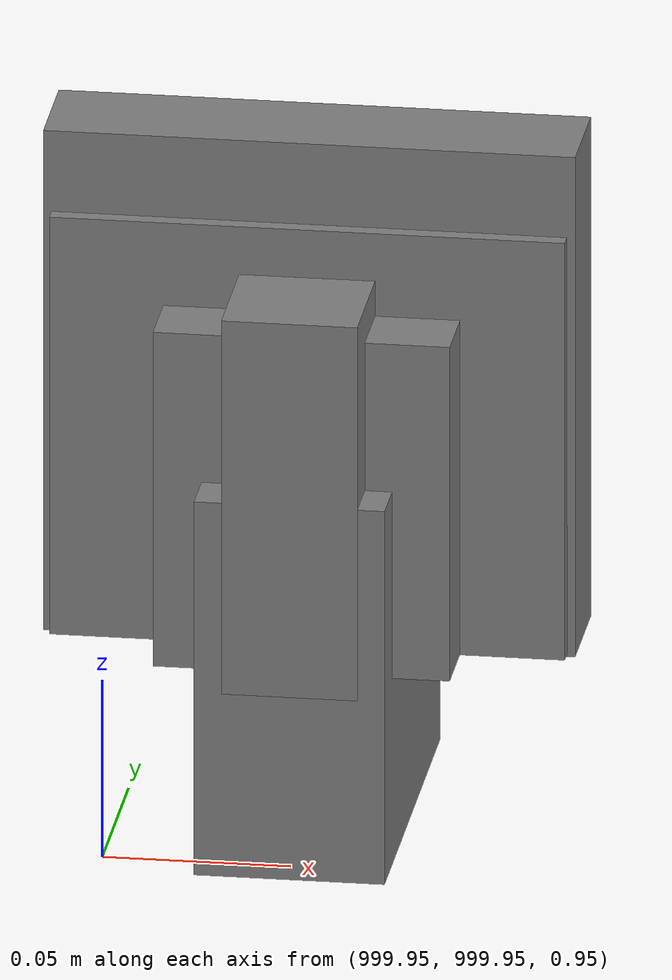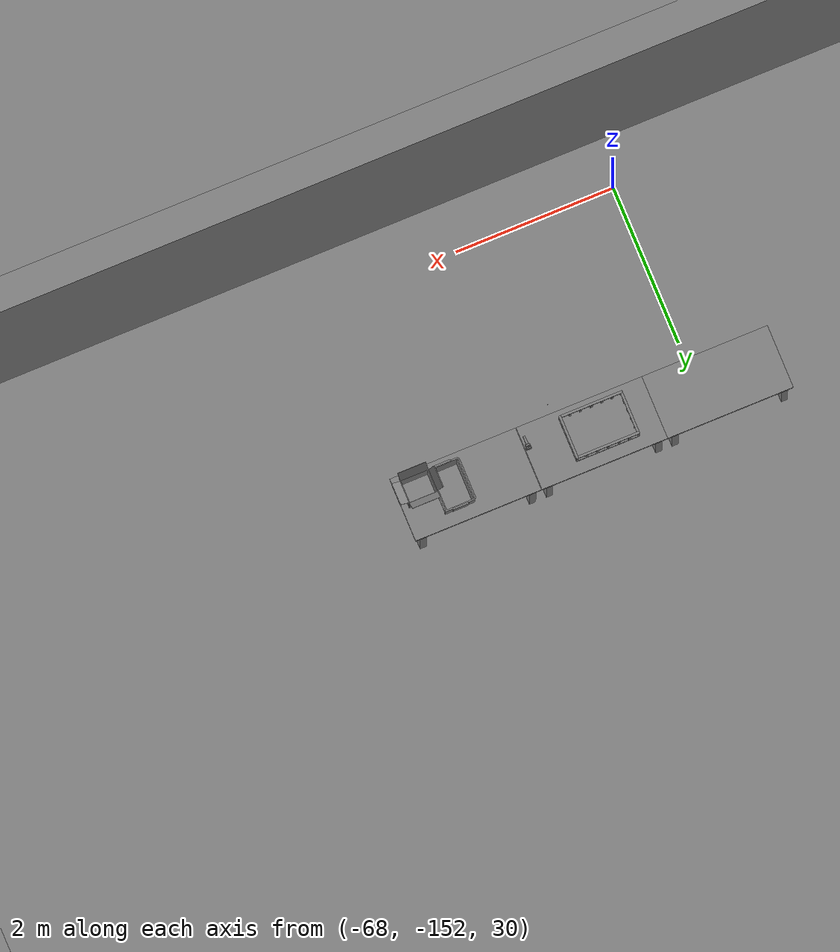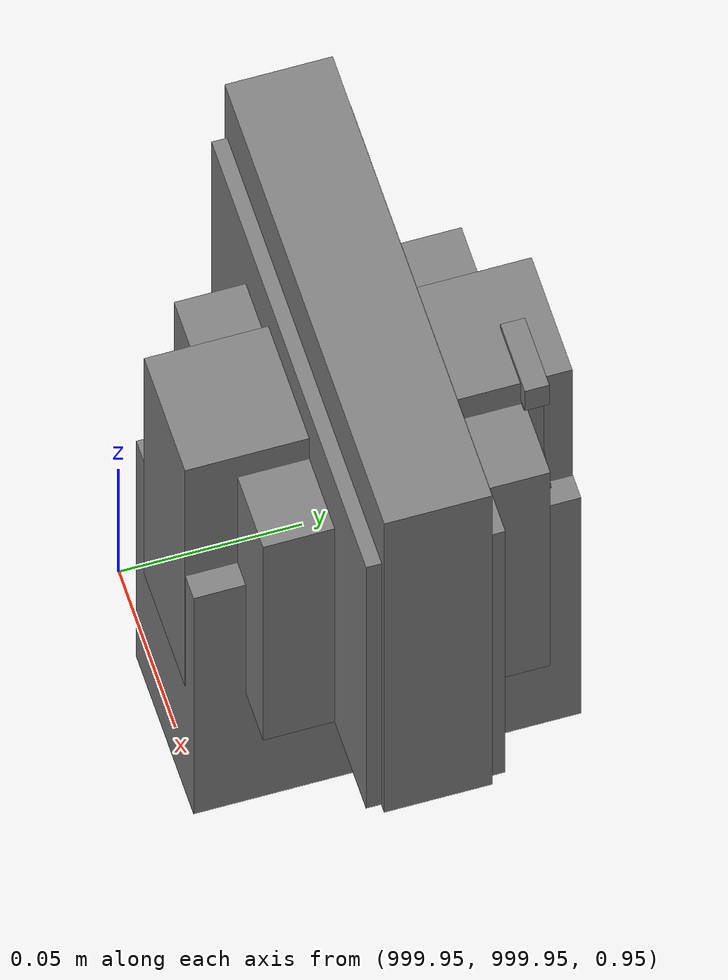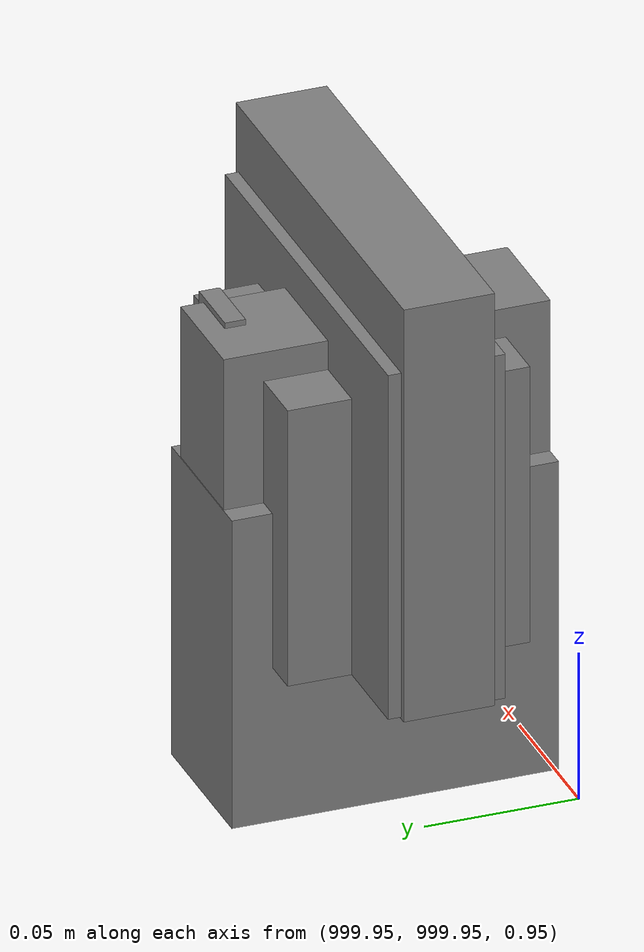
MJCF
<mujoco>
    <option gravity="0.000000000 0.000000000 -9.810000420" timestep="0.0049999999" integrator="implicitfast" density="1.225" viscosity="1.8000001e-05" noslip_iterations="10" iterations="100" sdf_iterations="50">
        <flag multiccd="disable"/>
    </option>
    <size memory="1000M"/>
    <compiler coordinate="local"/>
    <worldbody>
        <light cutoff="30" pos="0 1 1" dir="0 -1 -2"/>
        <light cutoff="30" pos="0 -1 1" dir="0 1 -2"/>
        <body pos="-64.866622925 -149.383972168 30.183746338" euler="89.999984741 89.999946594 0.000000000" name="openloong_gripper_2f85_fix_base_usda_bluebox_01">
            <geom contype="1" conaffinity="1" density="1000" type="box" material="" rgba="0.500000000 0.500000000 0.500000000 1.000000000" solimp="0.899999976 0.949999988 0.001000000" friction="1.000000000 0.005000000 0.000100000" solref="0.020000000 1.000000000" margin="0" condim="3" group="0" pos="0.276580811 0.187225342 0.000068665" quat="0.707106948 0.000077471 0.707106352 0.000077486" size="0.100000001 0.057999998 0.010000000" name="openloong_gripper_2f85_fix_base_usda_geom_D12F9AB6_A10D_4811_8D80_F7DEE4114F36"/>
            <geom contype="1" conaffinity="1" density="1000" type="box" material="" rgba="0.500000000 0.500000000 0.500000000 1.000000000" solimp="0.899999976 0.949999988 0.001000000" friction="1.000000000 0.005000000 0.000100000" solref="0.020000000 1.000000000" margin="0" condim="3" group="0" pos="0.000000000 0.002883911 0.000000000" quat="0.999999881 0.000000000 0.000000000 0.000000000" size="0.254000008 0.003000000 0.172000006" name="openloong_gripper_2f85_fix_base_usda_geom_70308CBA_F6C1_418D_9349_9EBB34A967DD"/>
            <geom contype="1" conaffinity="1" density="1000" type="box" material="" rgba="0.500000000 0.500000000 0.500000000 1.000000000" solimp="0.899999976 0.949999988 0.001000000" friction="1.000000000 0.005000000 0.000100000" solref="0.020000000 1.000000000" margin="0" condim="3" group="0" pos="0.000000000 0.124874115 0.173484802" quat="0.999796331 0.020176515 -0.000000015 0.000000030" size="0.259999990 0.119999997 0.007000000" name="openloong_gripper_2f85_fix_base_usda_geom_5386BA39_D30A_4BAA_96E0_B52379ABCAAD"/>
            <geom contype="1" conaffinity="1" density="1000" type="box" material="" rgba="0.500000000 0.500000000 0.500000000 1.000000000" solimp="0.899999976 0.949999988 0.001000000" friction="1.000000000 0.005000000 0.000100000" solref="0.020000000 1.000000000" margin="0" condim="3" group="0" pos="0.000000000 0.124874115 -0.173469543" quat="0.999796331 -0.020176545 -0.000000015 0.000000000" size="0.259999990 0.119999997 0.007000000" name="openloong_gripper_2f85_fix_base_usda_geom_EB9DA589_76D4_4717_8F63_386C59066F74"/>
            <geom contype="1" conaffinity="1" density="1000" type="box" material="" rgba="0.500000000 0.500000000 0.500000000 1.000000000" solimp="0.899999976 0.949999988 0.001000000" friction="1.000000000 0.005000000 0.000100000" solref="0.020000000 1.000000000" margin="0" condim="3" group="0" pos="0.000000000 0.214008331 0.188980103" quat="0.999912977 0.013176724 0.000000015 0.000000000" size="0.259999990 0.029999999 0.012500000" name="openloong_gripper_2f85_fix_base_usda_geom_BD366E8F_94FF_4097_A135_E385511E3F49"/>
            <geom contype="1" conaffinity="1" density="1000" type="box" material="" rgba="0.500000000 0.500000000 0.500000000 1.000000000" solimp="0.899999976 0.949999988 0.001000000" friction="1.000000000 0.005000000 0.000100000" solref="0.020000000 1.000000000" margin="0" condim="3" group="0" pos="-0.258361816 0.125289917 0.001876831" quat="0.702796936 -0.020792112 0.710783124 0.020769298" size="0.189999998 0.119999997 0.009000000" name="openloong_gripper_2f85_fix_base_usda_geom_B096B6F0_3981_436F_B491_0E24D9CEBB76"/>
            <geom contype="1" conaffinity="1" density="1000" type="box" material="" rgba="0.500000000 0.500000000 0.500000000 1.000000000" solimp="0.899999976 0.949999988 0.001000000" friction="1.000000000 0.005000000 0.000100000" solref="0.020000000 1.000000000" margin="0" condim="3" group="0" pos="0.000000000 0.214008331 -0.188980103" quat="0.999912977 -0.013176769 0.000000030 0.000000015" size="0.259999990 0.029999999 0.012500000" name="openloong_gripper_2f85_fix_base_usda_geom_DF6B5BC1_59D9_49E4_99DC_4E9BB260171B"/>
            <geom contype="1" conaffinity="1" density="1000" type="box" material="" rgba="0.500000000 0.500000000 0.500000000 1.000000000" solimp="0.899999976 0.949999988 0.001000000" friction="1.000000000 0.005000000 0.000100000" solref="0.020000000 1.000000000" margin="0" condim="3" group="0" pos="-0.276611328 0.187225342 0.000068665" quat="0.707106650 0.000077441 0.707106709 0.000077456" size="0.100000001 0.057999998 0.010000000" name="openloong_gripper_2f85_fix_base_usda_geom_CDB30B90_E8C4_4AB5_A3AD_A6D1996E5C41"/>
            <geom contype="1" conaffinity="1" density="1000" type="box" material="" rgba="0.500000000 0.500000000 0.500000000 1.000000000" solimp="0.899999976 0.949999988 0.001000000" friction="1.000000000 0.005000000 0.000100000" solref="0.020000000 1.000000000" margin="0" condim="3" group="0" pos="0.258331299 0.125289917 0.001876831" quat="0.702851415 0.018856421 0.710823774 -0.019329369" size="0.189999998 0.119999997 0.009000000" name="openloong_gripper_2f85_fix_base_usda_geom_DF7F25E0_8BA6_45BE_9D22_65FECF18E7F7"/>
            <freejoint name="openloong_gripper_2f85_fix_base_usda_bluebox_01_joint"/>
            <site size="0.005000000 0.005000000 0.005000000" rgba="0.500000000 0.500000000 0.500000000 1.000000000" pos="0.000000000 0.000000000 0.000000000" quat="0.999961913 0.008726534 0.000000000 0.000000000" group="0" type="sphere" name="openloong_gripper_2f85_fix_base_usda_bluebox_01site"/>
        </body>
        <body pos="-64.496299744 -149.491867065 30.235729218" euler="0.000000000 0.000000000 89.999946594" name="openloong_gripper_2f85_fix_base_usda_cardboardbox_01">
            <geom contype="1" conaffinity="1" density="1000" type="box" material="" rgba="0.500000000 0.500000000 0.500000000 1.000000000" solimp="0.899999976 0.949999988 0.001000000" friction="1.000000000 0.005000000 0.000100000" solref="0.020000000 1.000000000" margin="0" condim="3" group="0" pos="-0.003166199 -0.004086494 0.005052090" quat="1.000000000 0.000000000 0.000000000 0.000000000" size="0.142499998 0.177500010 0.005000000" name="openloong_gripper_2f85_fix_base_usda_geom_87332A7E_031E_447B_949D_F8843396ECFC"/>
            <geom contype="1" conaffinity="1" density="1000" type="box" material="" rgba="0.500000000 0.500000000 0.500000000 1.000000000" solimp="0.899999976 0.949999988 0.001000000" friction="1.000000000 0.005000000 0.000100000" solref="0.020000000 1.000000000" margin="0" condim="3" group="0" pos="-0.003166199 0.170316696 0.150570869" quat="1.000000000 0.000000000 0.000000000 0.000000000" size="0.142499998 0.005000000 0.149999991" name="openloong_gripper_2f85_fix_base_usda_geom_9744C06E_FA2D_4E44_9C96_72C10A8209EC"/>
            <geom contype="1" conaffinity="1" density="1000" type="box" material="" rgba="0.500000000 0.500000000 0.500000000 1.000000000" solimp="0.899999976 0.949999988 0.001000000" friction="1.000000000 0.005000000 0.000100000" solref="0.020000000 1.000000000" margin="0" condim="3" group="0" pos="-0.147399902 -0.005307198 0.150570869" quat="1.000000000 0.000000000 0.000000000 0.000000000" size="0.005000000 0.177500010 0.149999991" name="openloong_gripper_2f85_fix_base_usda_geom_2581B91C_BD6B_49C0_9BA2_48920BB1FFD6"/>
            <geom contype="1" conaffinity="1" density="1000" type="box" material="" rgba="0.500000000 0.500000000 0.500000000 1.000000000" solimp="0.899999976 0.949999988 0.001000000" friction="1.000000000 0.005000000 0.000100000" solref="0.020000000 1.000000000" margin="0" condim="3" group="0" pos="0.140275955 -0.005307198 0.150570869" quat="1.000000000 0.000000000 0.000000000 0.000000000" size="0.005000000 0.177500010 0.149999991" name="openloong_gripper_2f85_fix_base_usda_geom_7DFE02C7_BBB6_42AF_B11C_E259A6E58B33"/>
            <geom contype="1" conaffinity="1" density="1000" type="box" material="" rgba="0.500000000 0.500000000 0.500000000 1.000000000" solimp="0.899999976 0.949999988 0.001000000" friction="1.000000000 0.005000000 0.000100000" solref="0.020000000 1.000000000" margin="0" condim="3" group="0" pos="-0.003166199 -0.181550980 0.150570869" quat="1.000000000 0.000000000 0.000000000 0.000000000" size="0.142499998 0.005000000 0.149999991" name="openloong_gripper_2f85_fix_base_usda_geom_87A48262_B7DB_44CE_8B42_3BDCA9A4FC78"/>
            <freejoint name="openloong_gripper_2f85_fix_base_usda_cardboardbox_01_joint"/>
            <site size="0.005000000 0.005000000 0.005000000" rgba="0.500000000 0.500000000 0.500000000 1.000000000" pos="0.000000000 0.000000000 0.000000000" quat="0.999961913 0.008726535 0.000000000 0.000000000" group="0" type="sphere" name="openloong_gripper_2f85_fix_base_usda_site_814CB2DA_8192_48BF_8A2B_B1F5313DB23D"/>
            <body pos="0.139160156 -0.004048347 0.301930904" euler="-179.999954224 49.383502960 179.999954224" name="openloong_gripper_2f85_fix_base_usda_A1_006">
                <geom contype="1" conaffinity="1" density="1000" type="box" material="" rgba="0.500000000 0.500000000 0.500000000 1.000000000" solimp="0.899999976 0.949999988 0.001000000" friction="1.000000000 0.005000000 0.000100000" solref="0.020000000 1.000000000" margin="0" condim="3" group="0" pos="-0.071587563 0.000009537 0.001745224" quat="0.999999881 0.000000000 0.000000000 0.000000000" size="0.071249999 0.179999992 0.002500000" name="openloong_gripper_2f85_fix_base_usda_geom_D1919A37_7ED3_46ED_8119_D777BC94343C"/>
                <joint armature="0" stiffness="0.07" damping="0.0099999998" axis="0.000000 1.000000 0.000000" type="hinge" name="openloong_gripper_2f85_fix_base_usda_A1_006"/>
            </body>
            <body pos="-0.145902634 -0.004086494 0.301938057" euler="-180.000000000 -60.000011444 -180.000000000" name="openloong_gripper_2f85_fix_base_usda_A2_006">
                <geom contype="1" conaffinity="1" density="1000" type="box" material="" rgba="0.500000000 0.500000000 0.500000000 1.000000000" solimp="0.899999976 0.949999988 0.001000000" friction="1.000000000 0.005000000 0.000100000" solref="0.020000000 1.000000000" margin="0" condim="3" group="0" pos="0.071268082 0.000009537 0.002717972" quat="0.000002921 0.000000000 -0.000000030 0.999999881" size="0.071249999 0.179999992 0.002500000" name="openloong_gripper_2f85_fix_base_usda_geom_A35D2E56_C3B1_4D23_930D_2394F8472B36"/>
                <joint armature="0" stiffness="0.07" damping="0.0099999998" axis="0.000000 1.000000 0.000000" type="hinge" name="openloong_gripper_2f85_fix_base_usda_A2_006"/>
            </body>
            <body pos="-0.003385544 0.175991058 0.301930904" euler="-125.858116150 -0.000004561 0.000002331" name="openloong_gripper_2f85_fix_base_usda_B2_006">
                <geom contype="1" conaffinity="1" density="1000" type="box" material="" rgba="0.500000000 0.500000000 0.500000000 1.000000000" solimp="0.899999976 0.949999988 0.001000000" friction="1.000000000 0.005000000 0.000100000" solref="0.020000000 1.000000000" margin="0" condim="3" group="0" pos="0.000009537 -0.070939064 -0.002470016" quat="0.999614120 0.027776197 -0.000000015 0.000000030" size="0.137500003 0.064999998 0.005000000" name="openloong_gripper_2f85_fix_base_usda_geom_0A115102_7949_4492_9AFE_713011CBAF9D"/>
                <joint armature="0" stiffness="0.07" damping="0.0099999998" axis="1.000000 0.000000 0.000000" type="hinge" name="openloong_gripper_2f85_fix_base_usda_B2_006"/>
            </body>
            <body pos="-0.003385544 -0.184140205 0.301938057" euler="147.805557251 0.000000000 0.000000000" name="openloong_gripper_2f85_fix_base_usda_B1_006">
                <geom contype="1" conaffinity="1" density="1000" type="box" material="" rgba="0.500000000 0.500000000 0.500000000 1.000000000" solimp="0.899999976 0.949999988 0.001000000" friction="1.000000000 0.005000000 0.000100000" solref="0.020000000 1.000000000" margin="0" condim="3" group="0" pos="-0.000028610 0.070202351 -0.002703667" quat="0.999614179 -0.027776167 0.000000000 0.000000000" size="0.137500003 0.064999998 0.005000000" name="openloong_gripper_2f85_fix_base_usda_geom_14F71D8C_9439_4B28_986C_4F1CB696A213"/>
                <joint armature="0" stiffness="0.07" damping="0.0099999998" axis="1.000000 0.000000 0.000000" type="hinge" name="openloong_gripper_2f85_fix_base_usda_B1_006"/>
            </body>
        </body>
        <body pos="-65.882858276 -149.481979370 30.229999542" euler="-64.487716675 0.000000000 0.000000000" name="openloong_gripper_2f85_fix_base_usda_Barcode">
            <geom contype="1" conaffinity="1" density="1000" type="box" material="" rgba="0.500000000 0.500000000 0.500000000 1.000000000" solimp="0.899999976 0.949999988 0.001000000" friction="1.000000000 0.005000000 0.000100000" solref="0.020000000 1.000000000" margin="0" condim="3" group="0" pos="0.000000000 0.013038635 0.001419067" quat="0.000000000 0.000000000 0.000000000 1.000000119" size="0.034000002 0.010000000 0.017999999" name="openloong_gripper_2f85_fix_base_usda_geom_551D7CE5_6985_492D_9D24_1FA268D9537A"/>
            <geom contype="1" conaffinity="1" density="1000" type="box" material="" rgba="0.500000000 0.500000000 0.500000000 1.000000000" solimp="0.899999976 0.949999988 0.001000000" friction="1.000000000 0.005000000 0.000100000" solref="0.020000000 1.000000000" margin="0" condim="3" group="0" pos="0.000000000 -0.035301208 -0.007095337" quat="0.000000000 0.000000000 -0.043619365 0.999048233" size="0.028999999 0.010000000 0.020000000" name="openloong_gripper_2f85_fix_base_usda_geom_C3BCE962_0EB3_4AC0_91CA_7D777435AB3C"/>
            <geom contype="1" conaffinity="1" density="1000" type="box" material="" rgba="0.500000000 0.500000000 0.500000000 1.000000000" solimp="0.899999976 0.949999988 0.001000000" friction="1.000000000 0.005000000 0.000100000" solref="0.020000000 1.000000000" margin="0" condim="3" group="0" pos="0.000000000 -0.043411255 -0.011749268" quat="0.922262907 0.386563420 0.000000000 0.000000000" size="0.026000001 0.010000000 0.020000000" name="openloong_gripper_2f85_fix_base_usda_geom_C41E7FC8_3B9D_45C8_AD82_10EDE04B5185"/>
            <geom contype="1" conaffinity="1" density="1000" type="box" material="" rgba="0.500000000 0.500000000 0.500000000 1.000000000" solimp="0.899999976 0.949999988 0.001000000" friction="1.000000000 0.005000000 0.000100000" solref="0.020000000 1.000000000" margin="0" condim="3" group="0" pos="0.000000000 -0.016967773 -0.031860352" quat="0.000000000 0.000000000 0.000000000 1.000000119" size="0.008000000 0.010000000 0.013000000" name="openloong_gripper_2f85_fix_base_usda_geom_E61B0979_95DC_42E3_B72F_4D0D37CC774C"/>
            <geom contype="1" conaffinity="1" density="1000" type="box" material="" rgba="0.500000000 0.500000000 0.500000000 1.000000000" solimp="0.899999976 0.949999988 0.001000000" friction="1.000000000 0.005000000 0.000100000" solref="0.020000000 1.000000000" margin="0" condim="3" group="0" pos="0.000000000 -0.001869202 0.000312805" quat="0.953716993 0.300705761 0.000000000 0.000000000" size="0.032000002 0.010000000 0.018999999" name="openloong_gripper_2f85_fix_base_usda_geom_33580454_6D08_41BB_93BC_E74A7FCFA58C"/>
            <geom contype="1" conaffinity="1" density="1000" type="box" material="" rgba="0.500000000 0.500000000 0.500000000 1.000000000" solimp="0.899999976 0.949999988 0.001000000" friction="1.000000000 0.005000000 0.000100000" solref="0.020000000 1.000000000" margin="0" condim="3" group="0" pos="0.000000000 -0.019531250 -0.003173828" quat="0.953716993 0.300705761 0.000000000 0.000000000" size="0.030999999 0.010000000 0.020000000" name="openloong_gripper_2f85_fix_base_usda_geom_C20FD4FC_D4E4_4138_9486_BC407D0E3795"/>
            <geom contype="1" conaffinity="1" density="1000" type="box" material="" rgba="0.500000000 0.500000000 0.500000000 1.000000000" solimp="0.899999976 0.949999988 0.001000000" friction="1.000000000 0.005000000 0.000100000" solref="0.020000000 1.000000000" margin="0" condim="3" group="0" pos="0.000000000 -0.035301208 -0.007095337" quat="0.953716993 0.300705761 0.000000000 0.000000000" size="0.028999999 0.010000000 0.020000000" name="openloong_gripper_2f85_fix_base_usda_geom_CFAFBD4A_99F0_4D26_B0EE_7B4363894994"/>
            <geom contype="1" conaffinity="1" density="1000" type="box" material="" rgba="0.500000000 0.500000000 0.500000000 1.000000000" solimp="0.899999976 0.949999988 0.001000000" friction="1.000000000 0.005000000 0.000100000" solref="0.020000000 1.000000000" margin="0" condim="3" group="0" pos="0.000000000 -0.042617798 -0.071121216" quat="0.000000000 0.000000000 0.000000000 1.000000119" size="0.013000000 0.021000000 0.059999999" name="openloong_gripper_2f85_fix_base_usda_geom_2D4F150A_62C4_4A20_AC3F_04D062D4DFC3"/>
            <freejoint name="openloong_gripper_2f85_fix_base_usda_Barcode_joint"/>
            <site size="0.005000000 0.005000000 0.005000000" rgba="0.500000000 0.500000000 0.500000000 1.000000000" pos="0.000000000 0.000000000 0.000000000" quat="1.000000000 0.000000000 0.000000000 0.000000000" group="0" type="sphere" name="openloong_gripper_2f85_fix_base_usda_Barcode_site"/>
        </body>
        <body pos="-66.745018005 -149.392349243 30.184000015" euler="0.000000000 0.000000000 89.999946594" name="[22330034006673]_Basket_01">
            <geom contype="1" conaffinity="1" density="1000" type="box" material="" rgba="0.500000000 0.500000000 0.500000000 1.000000000" solimp="0.899999976 0.949999988 0.001000000" friction="1.000000000 0.005000000 0.000100000" solref="0.020000000 1.000000000" margin="0" condim="3" group="0" pos="-0.052425385 0.389207840 0.089787483" quat="0.707107008 0.000000000 0.000000000 0.707106411" size="0.014249999 0.014249999 0.059999999" name="[22330034006673]_geom_49A9868C_3EC2_45A3_93EE_CBC06227C4D9"/>
            <geom contype="1" conaffinity="1" density="1000" type="box" material="" rgba="0.500000000 0.500000000 0.500000000 1.000000000" solimp="0.899999976 0.949999988 0.001000000" friction="1.000000000 0.005000000 0.000100000" solref="0.020000000 1.000000000" margin="0" condim="3" group="0" pos="0.264015198 -0.133043289 0.089787483" quat="0.707107008 0.000000000 0.000000000 0.707106411" size="0.014249999 0.014249999 0.059999999" name="[22330034006673]_geom_2160DF59_800E_4AE8_8BA7_F42C1F0F75B6"/>
            <geom contype="1" conaffinity="1" density="1000" type="box" material="" rgba="0.500000000 0.500000000 0.500000000 1.000000000" solimp="0.899999976 0.949999988 0.001000000" friction="1.000000000 0.005000000 0.000100000" solref="0.020000000 1.000000000" margin="0" condim="3" group="0" pos="-0.264015198 -0.265548706 0.089793205" quat="0.707107008 0.000000000 0.000000000 0.707106411" size="0.014249999 0.014249999 0.059999999" name="[22330034006673]_geom_BDB974E2_31C9_4C17_99EF_23430C30104E"/>
            <geom contype="1" conaffinity="1" density="1000" type="box" material="" rgba="0.500000000 0.500000000 0.500000000 1.000000000" solimp="0.899999976 0.949999988 0.001000000" friction="1.000000000 0.005000000 0.000100000" solref="0.020000000 1.000000000" margin="0" condim="3" group="0" pos="-0.160263062 -0.389322281 0.089793205" quat="0.707107008 0.000000000 0.000000000 0.707106411" size="0.014249999 0.014249999 0.059999999" name="[22330034006673]_geom_173A7629_133C_4F0A_992F_16F07596EE1B"/>
            <geom contype="1" conaffinity="1" density="1000" type="box" material="" rgba="0.500000000 0.500000000 0.500000000 1.000000000" solimp="0.899999976 0.949999988 0.001000000" friction="1.000000000 0.005000000 0.000100000" solref="0.020000000 1.000000000" margin="0" condim="3" group="0" pos="0.162265778 -0.389322281 0.089787483" quat="0.707107008 0.000000000 0.000000000 0.707106411" size="0.014249999 0.014249999 0.059999999" name="[22330034006673]_geom_4D03DFE5_1229_4B40_81FD_13A0C795E56C"/>
            <geom contype="1" conaffinity="1" density="1000" type="box" material="" rgba="0.500000000 0.500000000 0.500000000 1.000000000" solimp="0.899999976 0.949999988 0.001000000" friction="1.000000000 0.005000000 0.000100000" solref="0.020000000 1.000000000" margin="0" condim="3" group="0" pos="0.264015198 0.389207840 0.089787483" quat="0.707107008 0.000000000 0.000000000 0.707106411" size="0.014249999 0.014249999 0.059999999" name="[22330034006673]_geom_65F30494_3BBF_45EC_841A_804B9B1B5628"/>
            <geom contype="1" conaffinity="1" density="1000" type="box" material="" rgba="0.500000000 0.500000000 0.500000000 1.000000000" solimp="0.899999976 0.949999988 0.001000000" friction="1.000000000 0.005000000 0.000100000" solref="0.020000000 1.000000000" margin="0" condim="3" group="0" pos="-0.264015198 -0.133043289 0.089793205" quat="0.707107008 0.000000000 0.000000000 0.707106411" size="0.014249999 0.014249999 0.059999999" name="[22330034006673]_geom_8EA49103_82A2_46D7_B49D_D005AEEB70B2"/>
            <geom contype="1" conaffinity="1" density="1000" type="box" material="" rgba="0.500000000 0.500000000 0.500000000 1.000000000" solimp="0.899999976 0.949999988 0.001000000" friction="1.000000000 0.005000000 0.000100000" solref="0.020000000 1.000000000" margin="0" condim="3" group="0" pos="-0.264026642 0.269256592 0.089793205" quat="0.707107008 0.000000000 0.000000000 0.707106411" size="0.014249999 0.014249999 0.059999999" name="[22330034006673]_geom_9BE63DEF_EA92_49FF_AED3_DFD1627B6EDC"/>
            <geom contype="1" conaffinity="1" density="1000" type="box" material="" rgba="0.500000000 0.500000000 0.500000000 1.000000000" solimp="0.899999976 0.949999988 0.001000000" friction="1.000000000 0.005000000 0.000100000" solref="0.020000000 1.000000000" margin="0" condim="3" group="0" pos="0.054462433 0.389207840 0.089787483" quat="0.707107008 0.000000000 0.000000000 0.707106411" size="0.014249999 0.014249999 0.059999999" name="[22330034006673]_geom_D060BBFB_B3BE_4A11_A172_877288BD6083"/>
            <geom contype="1" conaffinity="1" density="1000" type="box" material="" rgba="0.500000000 0.500000000 0.500000000 1.000000000" solimp="0.899999976 0.949999988 0.001000000" friction="1.000000000 0.005000000 0.000100000" solref="0.020000000 1.000000000" margin="0" condim="3" group="0" pos="0.054462433 -0.389322281 0.089787483" quat="0.707107008 0.000000000 0.000000000 0.707106411" size="0.014249999 0.014249999 0.059999999" name="[22330034006673]_geom_73F103D2_0367_4B32_B604_5FCFB09BFBC1"/>
            <geom contype="1" conaffinity="1" density="1000" type="box" material="" rgba="0.500000000 0.500000000 0.500000000 1.000000000" solimp="0.899999976 0.949999988 0.001000000" friction="1.000000000 0.005000000 0.000100000" solref="0.020000000 1.000000000" margin="0" condim="3" group="0" pos="0.264015198 0.269256592 0.089793205" quat="0.707107008 0.000000000 0.000000000 0.707106411" size="0.014249999 0.014249999 0.059999999" name="[22330034006673]_geom_701289C9_AE6B_4217_AEB6_897E6F0B0B35"/>
            <geom contype="1" conaffinity="1" density="1000" type="box" material="" rgba="0.500000000 0.500000000 0.500000000 1.000000000" solimp="0.899999976 0.949999988 0.001000000" friction="1.000000000 0.005000000 0.000100000" solref="0.020000000 1.000000000" margin="0" condim="3" group="0" pos="0.264015198 -0.389322281 0.089787483" quat="0.707107008 0.000000000 0.000000000 0.707106411" size="0.014249999 0.014249999 0.059999999" name="[22330034006673]_geom_8AF3186D_9EA5_4F54_986B_735E607843F9"/>
            <geom contype="1" conaffinity="1" density="1000" type="box" material="" rgba="0.500000000 0.500000000 0.500000000 1.000000000" solimp="0.899999976 0.949999988 0.001000000" friction="1.000000000 0.005000000 0.000100000" solref="0.020000000 1.000000000" margin="0" condim="3" group="0" pos="0.000000000 0.000000000 0.015998840" quat="0.707107008 0.000000000 0.000000000 0.707106411" size="0.403499991 0.279000014 0.015750000" name="[22330034006673]_geom_9E31E950_339F_404A_B368_CFC1BF58E5E8"/>
            <geom contype="1" conaffinity="1" density="1000" type="box" material="" rgba="0.500000000 0.500000000 0.500000000 1.000000000" solimp="0.899999976 0.949999988 0.001000000" friction="1.000000000 0.005000000 0.000100000" solref="0.020000000 1.000000000" margin="0" condim="3" group="0" pos="0.000000000 -0.389476776 0.163619041" quat="0.707107008 0.000000000 0.000000000 0.707106411" size="0.015000000 0.277500004 0.015750000" name="[22330034006673]_geom_184012B6_BF1B_476C_A767_2C8AB23CE8C5"/>
            <geom contype="1" conaffinity="1" density="1000" type="box" material="" rgba="0.500000000 0.500000000 0.500000000 1.000000000" solimp="0.899999976 0.949999988 0.001000000" friction="1.000000000 0.005000000 0.000100000" solref="0.020000000 1.000000000" margin="0" condim="3" group="0" pos="0.162265778 0.389207840 0.089787483" quat="0.707107008 0.000000000 0.000000000 0.707106411" size="0.014249999 0.014249999 0.059999999" name="[22330034006673]_geom_0CDA4754_ACFA_41FB_9F44_0BB08B758FF6"/>
            <geom contype="1" conaffinity="1" density="1000" type="box" material="" rgba="0.500000000 0.500000000 0.500000000 1.000000000" solimp="0.899999976 0.949999988 0.001000000" friction="1.000000000 0.005000000 0.000100000" solref="0.020000000 1.000000000" margin="0" condim="3" group="0" pos="0.000000000 0.389471054 0.163619041" quat="0.707107008 0.000000000 0.000000000 0.707106411" size="0.015000000 0.277500004 0.015750000" name="[22330034006673]_geom_A43A758C_2F48_4543_ACE1_B4FAADC13BB0"/>
            <geom contype="1" conaffinity="1" density="1000" type="box" material="" rgba="0.500000000 0.500000000 0.500000000 1.000000000" solimp="0.899999976 0.949999988 0.001000000" friction="1.000000000 0.005000000 0.000100000" solref="0.020000000 1.000000000" margin="0" condim="3" group="0" pos="-0.263511658 0.000000000 0.163619041" quat="0.707107008 0.000000000 0.000000000 0.707106411" size="0.403499991 0.015000000 0.015750000" name="[22330034006673]_geom_BC599ED6_6AC3_4ABC_B32D_1B45B08390DA"/>
            <geom contype="1" conaffinity="1" density="1000" type="box" material="" rgba="0.500000000 0.500000000 0.500000000 1.000000000" solimp="0.899999976 0.949999988 0.001000000" friction="1.000000000 0.005000000 0.000100000" solref="0.020000000 1.000000000" margin="0" condim="3" group="0" pos="-0.264015198 0.141334534 0.089793205" quat="0.707107008 0.000000000 0.000000000 0.707106411" size="0.014249999 0.014249999 0.059999999" name="[22330034006673]_geom_595107C6_7A12_443F_BF5C_DAD558A39CFB"/>
            <geom contype="1" conaffinity="1" density="1000" type="box" material="" rgba="0.500000000 0.500000000 0.500000000 1.000000000" solimp="0.899999976 0.949999988 0.001000000" friction="1.000000000 0.005000000 0.000100000" solref="0.020000000 1.000000000" margin="0" condim="3" group="0" pos="0.264015198 -0.265548706 0.089787483" quat="0.707107008 0.000000000 0.000000000 0.707106411" size="0.014249999 0.014249999 0.059999999" name="[22330034006673]_geom_B9AC181E_EAFC_4401_A4B6_5C56BE5EA278"/>
            <geom contype="1" conaffinity="1" density="1000" type="box" material="" rgba="0.500000000 0.500000000 0.500000000 1.000000000" solimp="0.899999976 0.949999988 0.001000000" friction="1.000000000 0.005000000 0.000100000" solref="0.020000000 1.000000000" margin="0" condim="3" group="0" pos="-0.160263062 0.389207840 0.089787483" quat="0.707107008 0.000000000 0.000000000 0.707106411" size="0.014249999 0.014249999 0.059999999" name="[22330034006673]_geom_D12CFC1F_76ED_4106_8A7D_6E083D71D251"/>
            <geom contype="1" conaffinity="1" density="1000" type="box" material="" rgba="0.500000000 0.500000000 0.500000000 1.000000000" solimp="0.899999976 0.949999988 0.001000000" friction="1.000000000 0.005000000 0.000100000" solref="0.020000000 1.000000000" margin="0" condim="3" group="0" pos="-0.052425385 -0.389322281 0.089787483" quat="0.707107008 0.000000000 0.000000000 0.707106411" size="0.014249999 0.014249999 0.059999999" name="[22330034006673]_geom_1FFD0BBA_6CB7_4C82_B2A1_694ACF06399C"/>
            <geom contype="1" conaffinity="1" density="1000" type="box" material="" rgba="0.500000000 0.500000000 0.500000000 1.000000000" solimp="0.899999976 0.949999988 0.001000000" friction="1.000000000 0.005000000 0.000100000" solref="0.020000000 1.000000000" margin="0" condim="3" group="0" pos="-0.264026642 -0.389322281 0.089793205" quat="0.707107008 0.000000000 0.000000000 0.707106411" size="0.014249999 0.014249999 0.059999999" name="[22330034006673]_geom_4197F10D_4C2D_4AF5_AC05_B7726AF281B8"/>
            <geom contype="1" conaffinity="1" density="1000" type="box" material="" rgba="0.500000000 0.500000000 0.500000000 1.000000000" solimp="0.899999976 0.949999988 0.001000000" friction="1.000000000 0.005000000 0.000100000" solref="0.020000000 1.000000000" margin="0" condim="3" group="0" pos="0.264015198 0.141334534 0.089787483" quat="0.707107008 0.000000000 0.000000000 0.707106411" size="0.014249999 0.014249999 0.059999999" name="[22330034006673]_geom_5AAED382_A4AF_4BED_9F9D_BB28CBBCE314"/>
            <geom contype="1" conaffinity="1" density="1000" type="box" material="" rgba="0.500000000 0.500000000 0.500000000 1.000000000" solimp="0.899999976 0.949999988 0.001000000" friction="1.000000000 0.005000000 0.000100000" solref="0.020000000 1.000000000" margin="0" condim="3" group="0" pos="-0.264015198 0.389207840 0.089793205" quat="0.707107008 0.000000000 0.000000000 0.707106411" size="0.014249999 0.014249999 0.059999999" name="[22330034006673]_geom_4813F507_9284_4DB4_946D_3DD7AC3AA5A5"/>
            <geom contype="1" conaffinity="1" density="1000" type="box" material="" rgba="0.500000000 0.500000000 0.500000000 1.000000000" solimp="0.899999976 0.949999988 0.001000000" friction="1.000000000 0.005000000 0.000100000" solref="0.020000000 1.000000000" margin="0" condim="3" group="0" pos="0.264015198 0.004480362 0.089787483" quat="0.707107008 0.000000000 0.000000000 0.707106411" size="0.014249999 0.014249999 0.059999999" name="[22330034006673]_geom_B5FBCB76_8A65_444B_B6EE_ABBCE129601F"/>
            <geom contype="1" conaffinity="1" density="1000" type="box" material="" rgba="0.500000000 0.500000000 0.500000000 1.000000000" solimp="0.899999976 0.949999988 0.001000000" friction="1.000000000 0.005000000 0.000100000" solref="0.020000000 1.000000000" margin="0" condim="3" group="0" pos="0.263694763 -0.000011444 0.163619041" quat="0.707107008 0.000000000 0.000000000 0.707106411" size="0.403499991 0.015000000 0.015750000" name="[22330034006673]_geom_069ED017_151B_441A_BBC3_E251B85158A3"/>
            <geom contype="1" conaffinity="1" density="1000" type="box" material="" rgba="0.500000000 0.500000000 0.500000000 1.000000000" solimp="0.899999976 0.949999988 0.001000000" friction="1.000000000 0.005000000 0.000100000" solref="0.020000000 1.000000000" margin="0" condim="3" group="0" pos="-0.264015198 0.004480362 0.089793205" quat="0.707107008 0.000000000 0.000000000 0.707106411" size="0.014249999 0.014249999 0.059999999" name="[22330034006673]_geom_843CF8A2_7F78_41B8_8E5B_96E13C0009B7"/>
            <freejoint name="[22330034006673]_joint_3B1CE6AA_28E4_4258_82AE_65FFD68E25A5"/>
        </body>
        <body pos="0.000000000 0.000000000 0.000000000" euler="0.000000000 0.000000000 0.000000000" name="Static Objects_Static Objects">
            <geom contype="1" conaffinity="1" density="1000" type="box" material="" rgba="0.500000000 0.500000000 0.500000000 1.000000000" solimp="0.899999976 0.949999988 0.001000000" friction="1.000000000 0.005000000 0.000100000" solref="0.020000000 1.000000000" margin="0" condim="3" group="0" pos="-67.544113159 -149.365814209 29.727830887" quat="0.500000417 0.499999970 0.499999553 0.499999970" size="0.381000012 0.319999993 0.041000001" name="Static Objects_geom_03EBDBA1_87B4_4422_B262_945390378865"/>
            <geom contype="1" conaffinity="1" density="1000" type="box" material="" rgba="0.500000000 0.500000000 0.500000000 1.000000000" solimp="0.899999976 0.949999988 0.001000000" friction="1.000000000 0.005000000 0.000100000" solref="0.020000000 1.000000000" margin="0" condim="3" group="0" pos="-68.239501953 -149.365814209 30.086868286" quat="0.500000417 0.499999970 0.499999553 0.499999970" size="0.370999992 0.039500002 0.745000005" name="Static Objects_geom_3BC64A6F_4B50_47E1_B2AE_73CFD575736C"/>
            <geom contype="1" conaffinity="1" density="1000" type="box" material="" rgba="0.500000000 0.500000000 0.500000000 1.000000000" solimp="0.899999976 0.949999988 0.001000000" friction="1.000000000 0.005000000 0.000100000" solref="0.020000000 1.000000000" margin="0" condim="3" group="0" pos="-68.239501953 -149.365814209 30.147235870" quat="0.500000417 0.499999970 0.499999553 0.499999970" size="0.400000006 0.022000000 0.800000012" name="Static Objects_geom_053834CC_92F7_4F8A_ABB1_2B29364B0B9E"/>
            <geom contype="1" conaffinity="1" density="1000" type="box" material="" rgba="0.500000000 0.500000000 0.500000000 1.000000000" solimp="0.899999976 0.949999988 0.001000000" friction="1.000000000 0.005000000 0.000100000" solref="0.020000000 1.000000000" margin="0" condim="3" group="0" pos="-68.934890747 -149.365814209 29.727830887" quat="0.500000417 0.499999970 0.499999553 0.499999970" size="0.381000012 0.319999993 0.041000001" name="Static Objects_geom_640F6E66_1FCC_4C45_8913_A93624BC7053"/>
            <geom contype="1" conaffinity="1" density="1000" type="box" material="" rgba="0.500000000 0.500000000 0.500000000 1.000000000" solimp="0.899999976 0.949999988 0.001000000" friction="1.000000000 0.005000000 0.000100000" solref="0.020000000 1.000000000" margin="0" condim="3" group="0" pos="-68.239501953 -149.365814209 29.561563492" quat="0.500000417 0.499999970 0.499999553 0.499999970" size="0.020000000 0.022000000 0.660000026" name="Static Objects_geom_87D157BB_30E4_49EE_B95B_7F65957D70C4"/>
            <geom contype="1" conaffinity="1" density="1000" type="box" material="" rgba="0.500000000 0.500000000 0.500000000 1.000000000" solimp="0.899999976 0.949999988 0.001000000" friction="1.000000000 0.005000000 0.000100000" solref="0.020000000 1.000000000" margin="0" condim="3" group="0" pos="-65.945671082 -149.365814209 29.727830887" quat="0.500000417 0.499999970 0.499999553 0.499999970" size="0.381000012 0.319999993 0.041000001" name="Static Objects_geom_11D958B5_26B2_4A50_973F_07A35CE6EF0A"/>
            <geom contype="1" conaffinity="1" density="1000" type="box" material="" rgba="0.500000000 0.500000000 0.500000000 1.000000000" solimp="0.899999976 0.949999988 0.001000000" friction="1.000000000 0.005000000 0.000100000" solref="0.020000000 1.000000000" margin="0" condim="3" group="0" pos="-66.641059875 -149.365814209 30.086868286" quat="0.500000417 0.499999970 0.499999553 0.499999970" size="0.370999992 0.039500002 0.745000005" name="Static Objects_geom_0EDA546D_8E69_4D7A_A164_A0228B690482"/>
            <geom contype="1" conaffinity="1" density="1000" type="box" material="" rgba="0.500000000 0.500000000 0.500000000 1.000000000" solimp="0.899999976 0.949999988 0.001000000" friction="1.000000000 0.005000000 0.000100000" solref="0.020000000 1.000000000" margin="0" condim="3" group="0" pos="-66.641059875 -149.365814209 30.147235870" quat="0.500000417 0.499999970 0.499999553 0.499999970" size="0.400000006 0.022000000 0.800000012" name="Static Objects_geom_58C6373B_DA7C_4DB8_AEBE_DA024359C2DA"/>
            <geom contype="1" conaffinity="1" density="1000" type="box" material="" rgba="0.500000000 0.500000000 0.500000000 1.000000000" solimp="0.899999976 0.949999988 0.001000000" friction="1.000000000 0.005000000 0.000100000" solref="0.020000000 1.000000000" margin="0" condim="3" group="0" pos="-67.336448669 -149.365814209 29.727830887" quat="0.500000417 0.499999970 0.499999553 0.499999970" size="0.381000012 0.319999993 0.041000001" name="Static Objects_geom_39160D90_8AAA_4F19_A534_A28C845E48C3"/>
            <geom contype="1" conaffinity="1" density="1000" type="box" material="" rgba="0.500000000 0.500000000 0.500000000 1.000000000" solimp="0.899999976 0.949999988 0.001000000" friction="1.000000000 0.005000000 0.000100000" solref="0.020000000 1.000000000" margin="0" condim="3" group="0" pos="-66.641059875 -149.365814209 29.561563492" quat="0.500000417 0.499999970 0.499999553 0.499999970" size="0.020000000 0.022000000 0.660000026" name="Static Objects_geom_6C5312FF_0D74_4B1F_B6BB_2E324FC868B5"/>
            <geom contype="1" conaffinity="1" density="1000" type="box" material="" rgba="0.500000000 0.500000000 0.500000000 1.000000000" solimp="0.899999976 0.949999988 0.001000000" friction="1.000000000 0.005000000 0.000100000" solref="0.020000000 1.000000000" margin="0" condim="3" group="0" pos="-64.338577271 -149.365814209 29.727830887" quat="0.500000417 0.499999970 0.499999553 0.499999970" size="0.381000012 0.319999993 0.041000001" name="Static Objects_geom_2E976E78_3E08_4311_9C5C_D43EF586DFA6"/>
            <geom contype="1" conaffinity="1" density="1000" type="box" material="" rgba="0.500000000 0.500000000 0.500000000 1.000000000" solimp="0.899999976 0.949999988 0.001000000" friction="1.000000000 0.005000000 0.000100000" solref="0.020000000 1.000000000" margin="0" condim="3" group="0" pos="-65.033966064 -149.365814209 30.086868286" quat="0.500000417 0.499999970 0.499999553 0.499999970" size="0.370999992 0.039500002 0.745000005" name="Static Objects_geom_F667347F_84F5_4F84_BBAE_A141EAFD3DEB"/>
            <geom contype="1" conaffinity="1" density="1000" type="box" material="" rgba="0.500000000 0.500000000 0.500000000 1.000000000" solimp="0.899999976 0.949999988 0.001000000" friction="1.000000000 0.005000000 0.000100000" solref="0.020000000 1.000000000" margin="0" condim="3" group="0" pos="-65.033966064 -149.365814209 30.147235870" quat="0.500000417 0.499999970 0.499999553 0.499999970" size="0.400000006 0.022000000 0.800000012" name="Static Objects_geom_C228AF15_9D98_4F9B_9AB5_385083260B91"/>
            <geom contype="1" conaffinity="1" density="1000" type="box" material="" rgba="0.500000000 0.500000000 0.500000000 1.000000000" solimp="0.899999976 0.949999988 0.001000000" friction="1.000000000 0.005000000 0.000100000" solref="0.020000000 1.000000000" margin="0" condim="3" group="0" pos="-65.729354858 -149.365814209 29.727830887" quat="0.500000417 0.499999970 0.499999553 0.499999970" size="0.381000012 0.319999993 0.041000001" name="Static Objects_geom_B6F63113_0A70_4ACB_A33C_AB706EE33F6B"/>
            <geom contype="1" conaffinity="1" density="1000" type="box" material="" rgba="0.500000000 0.500000000 0.500000000 1.000000000" solimp="0.899999976 0.949999988 0.001000000" friction="1.000000000 0.005000000 0.000100000" solref="0.020000000 1.000000000" margin="0" condim="3" group="0" pos="-65.033966064 -149.365814209 29.561563492" quat="0.500000417 0.499999970 0.499999553 0.499999970" size="0.020000000 0.022000000 0.660000026" name="Static Objects_geom_12D932DE_E0DC_416F_8812_9FE9A1909777"/>
            <geom contype="1" conaffinity="1" density="1000" type="box" material="" rgba="0.500000000 0.500000000 0.500000000 1.000000000" solimp="0.899999976 0.949999988 0.001000000" friction="1.000000000 0.005000000 0.000100000" solref="0.020000000 1.000000000" margin="0" condim="3" group="0" pos="-61.754566193 -137.853729248 33.906845093" quat="0.707107067 0.000000000 0.000000000 0.707106471" size="0.759999990 0.759999990 4.500000000" name="Static Objects_geom_ADB33988_E75A_413D_89A7_07CF372D2EB4"/>
            <geom contype="1" conaffinity="1" density="1000" type="box" material="" rgba="0.500000000 0.500000000 0.500000000 1.000000000" solimp="0.899999976 0.949999988 0.001000000" friction="1.000000000 0.005000000 0.000100000" solref="0.020000000 1.000000000" margin="0" condim="3" group="0" pos="-57.511135101 -144.927108765 31.707921982" quat="1.000000000 0.000000000 0.000000000 0.000000000" size="0.200000003 8.000000000 2.299999952" name="Static Objects_geom_F1958B9B_0C95_4BC3_A3F6_E64134FC6E72"/>
            <geom contype="1" conaffinity="1" density="1000" type="box" material="" rgba="0.500000000 0.500000000 0.500000000 1.000000000" solimp="0.899999976 0.949999988 0.001000000" friction="1.000000000 0.005000000 0.000100000" solref="0.020000000 1.000000000" margin="0" condim="3" group="0" pos="-80.517646790 -157.574050903 31.688196182" quat="0.707107067 0.000000000 0.000000000 0.707106471" size="0.600000024 0.600000024 2.299999952" name="Static Objects_geom_812CA197_F08A_4D21_9A58_92CBC7825B9B"/>
            <geom contype="1" conaffinity="1" density="1000" type="box" material="" rgba="0.500000000 0.500000000 0.500000000 1.000000000" solimp="0.899999976 0.949999988 0.001000000" friction="1.000000000 0.005000000 0.000100000" solref="0.020000000 1.000000000" margin="0" condim="3" group="0" pos="-80.711044312 -147.414932251 31.666158676" quat="1.000000000 0.000000000 0.000000000 0.000000000" size="0.200000003 10.000000000 2.299999952" name="Static Objects_geom_1AE2B038_8A7C_4BD2_B0BF_A823CED6D986"/>
            <geom contype="1" conaffinity="1" density="1000" type="box" material="" rgba="0.500000000 0.500000000 0.500000000 1.000000000" solimp="0.899999976 0.949999988 0.001000000" friction="1.000000000 0.005000000 0.000100000" solref="0.020000000 1.000000000" margin="0" condim="3" group="0" pos="-57.687217712 -137.434692383 31.688196182" quat="0.707107067 0.000000000 0.000000000 0.707106471" size="0.600000024 0.600000024 2.299999952" name="Static Objects_geom_657F9520_6D00_4FAC_A44A_8E53F8E01540"/>
            <geom contype="1" conaffinity="1" density="1000" type="box" material="" rgba="0.500000000 0.500000000 0.500000000 1.000000000" solimp="0.899999976 0.949999988 0.001000000" friction="1.000000000 0.005000000 0.000100000" solref="0.020000000 1.000000000" margin="0" condim="3" group="0" pos="-69.537033081 -140.263229370 31.714921951" quat="0.707107067 0.000000000 0.000000000 0.707106471" size="0.759999990 4.500000000 2.299999952" name="Static Objects_geom_C043FC89_9CC9_4327_9C5E_207488A81AA9"/>
            <geom contype="1" conaffinity="1" density="1000" type="box" material="" rgba="0.500000000 0.500000000 0.500000000 1.000000000" solimp="0.899999976 0.949999988 0.001000000" friction="1.000000000 0.005000000 0.000100000" solref="0.020000000 1.000000000" margin="0" condim="3" group="0" pos="-80.073638916 -137.853713989 33.906845093" quat="0.707107067 0.000000000 0.000000000 0.707106471" size="0.759999990 0.759999990 4.500000000" name="Static Objects_geom_0A16A8C1_99A7_4D95_A827_3A5B4C49E51C"/>
            <geom contype="1" conaffinity="1" density="1000" type="box" material="" rgba="0.500000000 0.500000000 0.500000000 1.000000000" solimp="0.899999976 0.949999988 0.001000000" friction="1.000000000 0.005000000 0.000100000" solref="0.020000000 1.000000000" margin="0" condim="3" group="0" pos="-73.406707764 -155.734664917 31.707921982" quat="1.000000000 0.000000000 0.000000000 0.000000000" size="0.200000003 3.000000000 2.299999952" name="Static Objects_geom_AA331078_538D_4E72_84E1_DF47E831AFC8"/>
            <geom contype="1" conaffinity="1" density="1000" type="box" material="" rgba="0.500000000 0.500000000 0.500000000 1.000000000" solimp="0.899999976 0.949999988 0.001000000" friction="1.000000000 0.005000000 0.000100000" solref="0.020000000 1.000000000" margin="0" condim="3" group="0" pos="-68.497543335 -137.448257446 31.707921982" quat="0.707107067 0.000000000 0.000000000 0.707106471" size="0.200000003 14.000000000 2.299999952" name="Static Objects_geom_C08ADB50_FCCA_4342_AF16_F17604656E82"/>
            <geom contype="1" conaffinity="1" density="1000" type="cylinder" material="" rgba="0.500000000 0.500000000 0.500000000 1.000000000" solimp="0.899999976 0.949999988 0.001000000" friction="1.000000000 0.005000000 0.000100000" solref="0.020000000 1.000000000" margin="0" condim="3" group="0" pos="-68.868522644 -142.134506226 31.711090088" quat="0.707107067 0.000000000 0.000000000 0.707106471" size="0.509999990 2.299999952 1.000000000" name="Static Objects_geom_E14D5C6B_A215_427B_8653_3CBEEA82B468"/>
            <geom contype="1" conaffinity="1" density="1000" type="plane" material="" rgba="0.500000000 0.500000000 0.500000000 1.000000000" solimp="0.899999976 0.949999988 0.001000000" friction="1.000000000 0.005000000 0.000100000" solref="0.020000000 1.000000000" margin="0" condim="3" group="0" pos="-72.873703003 -147.131927490 29.409669876" quat="1.000000000 0.000000000 0.000000000 0.000000000" size="18.000000000 14.000000000 1.000000000" name="Static Objects_geom_9FD13999_5235_4891_9634_B0F58780B608"/>
            <geom contype="1" conaffinity="1" density="1000" type="box" material="" rgba="0.500000000 0.500000000 0.500000000 1.000000000" solimp="0.899999976 0.949999988 0.001000000" friction="1.000000000 0.005000000 0.000100000" solref="0.020000000 1.000000000" margin="0" condim="3" group="0" pos="-79.943580627 -157.782272339 31.707921982" quat="0.707107067 0.000000000 0.000000000 0.707106471" size="0.200000003 7.000000000 2.299999952" name="Static Objects_geom_33886926_9EB2_42B2_8043_DD310E9502A8"/>
            <geom contype="1" conaffinity="1" density="1000" type="box" material="" rgba="0.500000000 0.500000000 0.500000000 1.000000000" solimp="0.899999976 0.949999988 0.001000000" friction="1.000000000 0.005000000 0.000100000" solref="0.020000000 1.000000000" margin="0" condim="3" group="0" pos="-65.421028137 -152.903442383 31.707921982" quat="0.707107067 0.000000000 0.000000000 0.707106471" size="0.200000003 7.800000191 2.299999952" name="Static Objects_geom_8612F34C_1710_4EEC_A665_2113F0548DAB"/>
            <geom contype="1" conaffinity="1" density="1000" type="box" material="" rgba="0.500000000 0.500000000 0.500000000 1.000000000" solimp="0.899999976 0.949999988 0.001000000" friction="1.000000000 0.005000000 0.000100000" solref="0.020000000 1.000000000" margin="0" condim="3" group="0" pos="-74.776908875 -149.964416504 31.688196182" quat="1.000000000 0.000000000 0.000000000 0.000000000" size="0.600000024 0.409999996 2.299999952" name="Static Objects_geom_2399BAD5_7A88_40C5_8D8A_622CC4EC94AE"/>
            <geom contype="1" conaffinity="1" density="1000" type="cylinder" material="" rgba="0.500000000 0.500000000 0.500000000 1.000000000" solimp="0.899999976 0.949999988 0.001000000" friction="1.000000000 0.005000000 0.000100000" solref="0.020000000 1.000000000" margin="0" condim="3" group="0" pos="-60.161884308 -142.134506226 31.711090088" quat="0.707107067 0.000000000 0.000000000 0.707106471" size="0.509999990 2.299999952 1.000000000" name="Static Objects_geom_D7B42337_6655_4768_8800_AE700C6E0170"/>
            <geom contype="1" conaffinity="1" density="1000" type="cylinder" material="" rgba="0.500000000 0.500000000 0.500000000 1.000000000" solimp="0.899999976 0.949999988 0.001000000" friction="1.000000000 0.005000000 0.000100000" solref="0.020000000 1.000000000" margin="0" condim="3" group="0" pos="-75.382453918 -149.963455200 31.711090088" quat="0.707107067 0.000000000 0.000000000 0.707106471" size="0.409999996 2.299999952 1.000000000" name="Static Objects_geom_FA95EF6D_0B54_4FE4_BF0A_5052D748A8EE"/>
            <geom contype="1" conaffinity="1" density="1000" type="cylinder" material="" rgba="0.500000000 0.500000000 0.500000000 1.000000000" solimp="0.899999976 0.949999988 0.001000000" friction="1.000000000 0.005000000 0.000100000" solref="0.020000000 1.000000000" margin="0" condim="3" group="0" pos="-74.154960632 -149.963455200 31.711090088" quat="0.707107067 0.000000000 0.000000000 0.707106471" size="0.409999996 2.299999952 1.000000000" name="Static Objects_geom_25E9EE0E_D3E1_4F20_AAF9_80BA7A0DE9AA"/>
            <geom contype="1" conaffinity="1" density="1000" type="cylinder" material="" rgba="0.500000000 0.500000000 0.500000000 1.000000000" solimp="0.899999976 0.949999988 0.001000000" friction="1.000000000 0.005000000 0.000100000" solref="0.020000000 1.000000000" margin="0" condim="3" group="0" pos="-77.566612244 -142.134506226 31.711090088" quat="0.707107067 0.000000000 0.000000000 0.707106471" size="0.509999990 2.299999952 1.000000000" name="Static Objects_geom_FB81A506_BC8C_40CC_BC73_7C475A591B1A"/>
        </body>
        <body pos="-66.209136963 -149.701995850 31.166507721" euler="-5.449571133 -65.357887268 78.096176147" mocap="true" name="spotlight4_SpotLight"/>
        <body pos="1000.000000000 1000.000000000 1.000000000" euler="0.000000000 0.000000000 180.000000000" name="openloong_gripper_2f85_fix_base_usda_battery_01">
            <geom contype="1" conaffinity="1" density="1000" type="box" material="" rgba="0.500000000 0.500000000 0.500000000 1.000000000" solimp="0.899999976 0.949999988 0.001000000" friction="1.000000000 0.005000000 0.000100000" solref="0.020000000 1.000000000" margin="0" condim="3" group="0" pos="-0.011123657 -0.041940309 0.101691343" quat="1.000000000 0.000000000 0.000000000 0.000000000" size="0.010800000 0.003375000 0.004725000" name="openloong_gripper_2f85_fix_base_usda_geom_B9575709_215A_4C83_9386_2B237A228F4F"/>
            <geom contype="1" conaffinity="1" density="1000" type="box" material="" rgba="0.500000000 0.500000000 0.500000000 1.000000000" solimp="0.899999976 0.949999988 0.001000000" friction="1.000000000 0.005000000 0.000100000" solref="0.020000000 1.000000000" margin="0" condim="3" group="0" pos="-0.010876465 -0.044247437 0.047066893" quat="0.998702705 -0.050920475 0.000000000 0.000000000" size="0.009450001 0.002700000 0.024975000" name="openloong_gripper_2f85_fix_base_usda_geom_6CC402DF_D1D8_4E30_820B_B475F64559D3"/>
            <geom contype="1" conaffinity="1" density="1000" type="box" material="" rgba="0.500000000 0.500000000 0.500000000 1.000000000" solimp="0.899999976 0.949999988 0.001000000" friction="1.000000000 0.005000000 0.000100000" solref="0.020000000 1.000000000" margin="0" condim="3" group="0" pos="-0.001235962 -0.000659180 0.047381196" quat="1.000000000 0.000000000 0.000000000 0.000000000" size="0.039420001 0.039150000 0.047250003" name="openloong_gripper_2f85_fix_base_usda_geom_9F56ACD4_AF10_4CC6_8B18_837FB519305C"/>
            <geom contype="1" conaffinity="1" density="1000" type="box" material="" rgba="0.500000000 0.500000000 0.500000000 1.000000000" solimp="0.899999976 0.949999988 0.001000000" friction="1.000000000 0.005000000 0.000100000" solref="0.020000000 1.000000000" margin="0" condim="3" group="0" pos="-0.010876465 -0.039138794 0.009851727" quat="1.000000000 0.000000000 0.000000000 0.000000000" size="0.009450001 0.010800000 0.013500000" name="openloong_gripper_2f85_fix_base_usda_geom_BD4FCF22_104E_43A1_BFC0_06BBC27272B3"/>
            <geom contype="1" conaffinity="1" density="1000" type="box" material="" rgba="0.500000000 0.500000000 0.500000000 1.000000000" solimp="0.899999976 0.949999988 0.001000000" friction="1.000000000 0.005000000 0.000100000" solref="0.020000000 1.000000000" margin="0" condim="3" group="0" pos="-0.010876465 -0.041528322 0.071508206" quat="1.000000000 0.000000000 0.000000000 0.000000000" size="0.009450001 0.002700000 0.027000001" name="openloong_gripper_2f85_fix_base_usda_geom_99E6B218_F596_42D8_A726_8493E8A63E37"/>
            <freejoint name="openloong_gripper_2f85_fix_base_usda_battery_01_joint"/>
            <site size="0.005000000 0.005000000 0.005000000" rgba="0.500000000 0.500000000 0.500000000 1.000000000" pos="0.000000000 0.000000000 0.000000000" quat="0.999961913 0.008726500 0.000000000 0.000000000" group="0" type="sphere" name="openloong_gripper_2f85_fix_base_usda_battery_01site"/>
        </body>
        <body pos="-66.138900757 -149.157974243 31.171924591" euler="164.207504272 16.707675934 -173.825393677" mocap="true" name="spotlight3_SpotLight"/>
        <body pos="1000.000000000 1000.000000000 1.000000000" euler="0.000000000 0.000000000 180.000000000" name="openloong_gripper_2f85_fix_base_usda_cpu_fan">
            <geom contype="1" conaffinity="1" density="1000" type="box" material="" rgba="0.500000000 0.500000000 0.500000000 1.000000000" solimp="0.899999976 0.949999988 0.001000000" friction="1.000000000 0.005000000 0.000100000" solref="0.020000000 1.000000000" margin="0" condim="3" group="0" pos="0.000000000 0.000000000 0.070034981" quat="0.000000000 0.000000000 0.000000000 1.000000000" size="0.070700005 0.014699999 0.070700005" name="openloong_gripper_2f85_fix_base_usda_geom_0451FCBC_1624_4BC4_8242_4E7CC6A9D206"/>
            <freejoint name="openloong_gripper_2f85_fix_base_usda_cpu_fan_joint"/>
            <site size="0.005000000 0.005000000 0.005000000" rgba="0.500000000 0.500000000 0.500000000 1.000000000" pos="0.000000000 0.000000000 0.000000000" quat="0.999961913 0.008726535 0.000000000 0.000000000" group="0" type="sphere" name="openloong_gripper_2f85_fix_base_usda_cpu_fancsite"/>
        </body>
        <body pos="1000.000000000 1000.000000000 1.000000000" euler="0.000000000 0.000000000 180.000000000" name="openloong_gripper_2f85_fix_base_usda_wifi_box">
            <geom contype="1" conaffinity="1" density="1000" type="box" material="" rgba="0.500000000 0.500000000 0.500000000 1.000000000" solimp="0.899999976 0.949999988 0.001000000" friction="1.000000000 0.005000000 0.000100000" solref="0.020000000 1.000000000" margin="0" condim="3" group="0" pos="0.000000000 0.000000000 0.058978677" quat="0.000000000 0.000000047 0.000000000 1.000000000" size="0.068499997 0.018999999 0.059000000" name="openloong_gripper_2f85_fix_base_usda_geom_615FA91B_A015_4DAA_BA09_487B7CCC12A5"/>
            <freejoint name="openloong_gripper_2f85_fix_base_usda_wifi_box_joint"/>
            <site size="0.005000000 0.005000000 0.005000000" rgba="0.500000000 0.500000000 0.500000000 1.000000000" pos="0.000000000 0.000000000 0.000000000" quat="0.999961913 0.008726500 0.000000000 0.000000000" group="0" type="sphere" name="openloong_gripper_2f85_fix_base_usda_wifi_boxsite"/>
        </body>
        <body pos="1000.000000000 1000.000000000 1.000000000" euler="0.000011953 0.000005123 -179.999984741" name="openloong_gripper_2f85_fix_base_usda_intel_box">
            <geom contype="1" conaffinity="1" density="1000" type="box" material="" rgba="0.500000000 0.500000000 0.500000000 1.000000000" solimp="0.899999976 0.949999988 0.001000000" friction="1.000000000 0.005000000 0.000100000" solref="0.020000000 1.000000000" margin="0" condim="3" group="0" pos="0.000000000 -0.000067139 0.000082284" quat="0.707106709 0.000000225 0.000000253 0.707106650" size="0.052800003 0.025300000 0.052800003" name="openloong_gripper_2f85_fix_base_usda_geom_F4EDB975_1FBF_467A_A581_EAA0C43771E0"/>
            <freejoint name="openloong_gripper_2f85_fix_base_usda_intel_box_joint"/>
            <site size="0.005000000 0.005000000 0.005000000" rgba="0.500000000 0.500000000 0.500000000 1.000000000" pos="0.000000000 0.000000000 0.000000000" quat="0.999961913 0.008726500 0.000000000 0.000000000" group="0" type="sphere" name="openloong_gripper_2f85_fix_base_usda_intel_boxsite"/>
        </body>
        <body pos="1000.000000000 999.999938965 1.000000000" euler="0.000000000 0.000000000 180.000000000" name="openloong_gripper_2f85_fix_base_usda_intelcore_i5">
            <geom contype="1" conaffinity="1" density="1000" type="box" material="" rgba="0.500000000 0.500000000 0.500000000 1.000000000" solimp="0.899999976 0.949999988 0.001000000" friction="1.000000000 0.005000000 0.000100000" solref="0.020000000 1.000000000" margin="0" condim="3" group="0" pos="0.000000000 0.000000000 0.051722717" quat="0.707106709 0.000000000 0.000000000 -0.707106769" size="0.052800000 0.018080002 0.052800000" name="openloong_gripper_2f85_fix_base_usda_geom_091BD5B0_480D_460D_83AD_01FE5BD3135E"/>
            <freejoint name="openloong_gripper_2f85_fix_base_usda_intelcore_i5_joint"/>
            <site size="0.005000000 0.005000000 0.005000000" rgba="0.500000000 0.500000000 0.500000000 1.000000000" pos="0.000000000 0.000000000 0.000000000" quat="0.999961913 0.008726534 0.000000000 0.000000000" group="0" type="sphere" name="openloong_gripper_2f85_fix_base_usda_intelcore_i5site"/>
        </body>
        <body pos="-66.287788391 -148.846817017 31.170116425" euler="169.068984985 -85.230613708 116.007614136" mocap="true" name="spotlight2_SpotLight"/>
        <body pos="-66.291030884 -149.869689941 29.018842697" euler="0.000000000 0.000000000 89.999946594" mocap="true" name="openloong_gripper_2f85_fix_base_usda_leftHandMocap"/>
        <body pos="-66.291030884 -149.869689941 29.018842697" euler="0.000000000 0.000000000 89.999946594" mocap="true" name="openloong_gripper_2f85_fix_base_usda_rightHandMocap"/>
        <body pos="-66.291030884 -149.869689941 30.218843460" euler="0.000000000 0.000000000 89.999946594" name="openloong_gripper_2f85_fix_base_usda_base_link">
            <geom contype="1" conaffinity="1" density="1000" type="mesh" material="" rgba="0.783999979 0.783999979 0.783999979 1.000000000" solimp="0.899999976 0.949999988 0.001000000" friction="1.000000000 0.005000000 0.000100000" solref="0.020000000 1.000000000" margin="0" condim="3" group="3" mesh="base_link" pos="0.000000000 0.000000000 0.000000000" quat="1.000000000 0.000000000 0.000000000 0.000000000" size="1.000000000 1.000000000 1.000000000" name="openloong_gripper_2f85_fix_base_usda__geom_7_A4DB74A5_3E6E_499C_BDB8_200432C40207"/>
            <site size="0.005000000 0.005000000 0.005000000" rgba="0.500000000 0.500000000 0.500000000 1.000000000" pos="0.000000000 0.000000000 0.000000000" quat="1.000000000 0.000000000 0.000000000 0.000000000" group="0" type="sphere" name="openloong_gripper_2f85_fix_base_usda_imu"/>
            <inertial mass="22.447001" pos="-0.005664100 -0.001336700 0.238289997" diaginertia="0.374352545 0.277180195 0.220617250" quat="0.999247074 0.035235517 -0.015086859 0.006023135"/>
            <body pos="0.000000000 0.000000000 0.299997330" euler="0.000000000 0.000000000 0.000000000" name="openloong_gripper_2f85_fix_base_usda_dummy_body">
                <geom contype="1" conaffinity="1" density="1000" type="sphere" material="" rgba="0.783999979 0.783999979 0.783999979 1.000000000" solimp="0.899999976 0.949999988 0.001000000" friction="1.000000000 0.005000000 0.000100000" solref="0.020000000 1.000000000" margin="0" condim="3" group="3" pos="0.000000000 0.000000000 0.000000000" quat="1.000000000 0.000000000 0.000000000 0.000000000" size="0.010000000 0.000000000 0.000000000" name="openloong_gripper_2f85_fix_base_usda__geom_8_0C960D28_A3DB_41B9_8F05_E77DAA0C507C"/>
                <joint armature="0.0099999998" stiffness="0" damping="0.1" axis="0.000000 0.000000 1.000000" type="hinge" name="openloong_gripper_2f85_fix_base_usda_dummy_joint"/>
                <site size="0.010000000 0.005000000 0.005000000" rgba="0.500000000 0.500000000 0.500000000 1.000000000" pos="0.000000000 0.000000000 0.000000000" quat="1.000000000 0.000000000 0.000000000 0.000000000" group="3" type="sphere" name="openloong_gripper_2f85_fix_base_usda_dummy_site"/>
            </body>
            <body pos="0.009002686 0.000000000 0.406400681" euler="0.000000000 0.000000000 0.000000000" name="openloong_gripper_2f85_fix_base_usda_Link_head_yaw">
                <geom contype="1" conaffinity="1" density="1000" type="mesh" material="" rgba="0.783999979 0.783999979 0.783999979 1.000000000" solimp="0.899999976 0.949999988 0.001000000" friction="1.000000000 0.005000000 0.000100000" solref="0.020000000 1.000000000" margin="0" condim="3" group="3" mesh="Link_head_yaw" pos="0.000000000 0.000000000 0.000000000" quat="1.000000000 0.000000000 0.000000000 0.000000000" size="1.000000000 1.000000000 1.000000000" name="openloong_gripper_2f85_fix_base_usda__geom_10_F8DD5AE4_F0F8_45AA_BBC9_29D5E428A501"/>
                <inertial mass="0.84249002" pos="0.000000000 -0.002081400 0.044801001" diaginertia="0.000700588 0.000629000 0.000553812" quat="0.706933022 -0.015675601 0.015677100 0.706933022"/>
                <body pos="0.000000000 -0.034599304 0.048500061" euler="0.000000000 0.000000000 0.000000000" name="openloong_gripper_2f85_fix_base_usda_Link_head_pitch">
                    <geom contype="1" conaffinity="1" density="1000" type="mesh" material="" rgba="0.783999979 0.783999979 0.783999979 1.000000000" solimp="0.899999976 0.949999988 0.001000000" friction="1.000000000 0.005000000 0.000100000" solref="0.020000000 1.000000000" margin="0" condim="3" group="3" mesh="Link_head_pitch" pos="0.000000000 0.000000000 0.000000000" quat="1.000000000 0.000000000 0.000000000 0.000000000" size="1.000000000 1.000000000 1.000000000" name="openloong_gripper_2f85_fix_base_usda__geom_12_AD05A69C_6C77_4285_8D46_2C11E8911015"/>
                    <inertial mass="1.3943" pos="0.020569000 0.033004001 0.125000000" diaginertia="0.006381400 0.006289940 0.004481460" quat="0.973390222 0.008406822 0.228157058 0.019624906"/>
                    <body pos="0.000000000 0.029998779 0.000000000" euler="0.000000000 0.000000000 0.000000000" name="openloong_gripper_2f85_fix_base_usda_neck_center_body">
                        <site size="0.010000000 0.005000000 0.005000000" rgba="0.500000000 0.500000000 0.500000000 1.000000000" pos="0.000000000 0.000000000 0.000000000" quat="1.000000000 0.000000000 0.000000000 0.000000000" group="3" type="sphere" name="openloong_gripper_2f85_fix_base_usda_neck_center_site"/>
                        <body pos="0.020004272 0.000000000 0.149999619" euler="-0.000002229 39.998176575 -90.000205994" name="openloong_gripper_2f85_fix_base_usda_camera_head">
                            <site size="0.010000000 0.005000000 0.005000000" rgba="0.500000000 0.500000000 0.500000000 1.000000000" pos="0.000000000 0.000000000 0.000000000" quat="1.000000000 0.000000000 0.000000000 0.000000000" group="3" type="sphere" name="openloong_gripper_2f85_fix_base_usda_camera_head_site"/>
                        </body>
                    </body>
                </body>
            </body>
            <body pos="0.003997803 -0.161598206 0.392200470" euler="0.000000000 0.000000000 0.000000000" name="openloong_gripper_2f85_fix_base_usda_Link_arm_r_01">
                <geom contype="1" conaffinity="1" density="1000" type="mesh" material="" rgba="0.783999979 0.783999979 0.783999979 1.000000000" solimp="0.899999976 0.949999988 0.001000000" friction="1.000000000 0.005000000 0.000100000" solref="0.020000000 1.000000000" margin="0" condim="3" group="3" mesh="Link_arm_r_01" pos="0.000000000 0.000000000 0.000000000" quat="1.000000000 0.000000000 0.000000000 0.000000000" size="1.000000000 1.000000000 1.000000000" name="openloong_gripper_2f85_fix_base_usda__geom_14_B9F76B22_2480_473C_95F2_412AFA09C55A"/>
                <joint armature="0.0099999998" stiffness="0" damping="1" axis="0.000000 -1.000000 0.000000" limited="true" range="-170.000015259 170.000015259" type="hinge" name="openloong_gripper_2f85_fix_base_usda_J_arm_r_01"/>
                <inertial mass="0.75641" pos="0.004494600 -0.038293999 -0.000001874" diaginertia="0.000842990 0.000803050 0.000587120" quat="-0.000163502 0.707098067 0.000812463 0.707115054"/>
                <body pos="-0.041992188 -0.041000366 0.000000000" euler="0.000000000 0.000000000 0.000000000" name="openloong_gripper_2f85_fix_base_usda_Link_arm_r_02">
                    <geom contype="1" conaffinity="1" density="1000" type="mesh" material="" rgba="0.783999979 0.783999979 0.783999979 1.000000000" solimp="0.899999976 0.949999988 0.001000000" friction="1.000000000 0.005000000 0.000100000" solref="0.020000000 1.000000000" margin="0" condim="3" group="3" mesh="Link_arm_r_02" pos="0.000000000 0.000000000 0.000000000" quat="1.000000000 0.000000000 0.000000000 0.000000000" size="1.000000000 1.000000000 1.000000000" name="openloong_gripper_2f85_fix_base_usda__geom_16_427CFEFE_F826_43E5_98C4_77BD556DF3CA"/>
                    <joint armature="0.0099999998" stiffness="0" damping="1" axis="-1.000000 0.000000 0.000000" limited="true" range="-105.000244141 105.000244141" type="hinge" name="openloong_gripper_2f85_fix_base_usda_J_arm_r_02"/>
                    <inertial mass="0.98500001" pos="0.041999999 -0.067430697 0.000000000" diaginertia="0.002262690 0.001730990 0.001154020" quat="0.500000000 0.500000000 -0.500000000 0.500000000"/>
                    <body pos="0.041992188 -0.122596741 0.000000000" euler="0.000000000 0.000000000 0.000000000" name="openloong_gripper_2f85_fix_base_usda_Link_arm_r_03">
                        <geom contype="1" conaffinity="1" density="1000" type="mesh" material="" rgba="0.783999979 0.783999979 0.783999979 1.000000000" solimp="0.899999976 0.949999988 0.001000000" friction="1.000000000 0.005000000 0.000100000" solref="0.020000000 1.000000000" margin="0" condim="3" group="3" mesh="Link_arm_r_03" pos="0.000000000 0.000000000 0.000000000" quat="1.000000000 0.000000000 0.000000000 0.000000000" size="1.000000000 1.000000000 1.000000000" name="openloong_gripper_2f85_fix_base_usda__geom_18_16BDD502_533D_43BB_87B4_78077393DEA4"/>
                        <joint armature="0.0099999998" stiffness="0" damping="1" axis="0.000000 -1.000000 0.000000" limited="true" range="-170.000015259 170.000015259" type="hinge" name="openloong_gripper_2f85_fix_base_usda_J_arm_r_03"/>
                        <inertial mass="0.95899999" pos="-0.001413580 -0.164663002 0.020757901" diaginertia="0.002101340 0.002064590 0.000754802" quat="0.560480952 0.454391927 -0.443732947 0.531497955"/>
                        <body pos="0.035293579 -0.177406311 0.023998260" euler="0.000000000 0.000000000 0.000000000" name="openloong_gripper_2f85_fix_base_usda_Link_arm_r_04">
                            <geom contype="1" conaffinity="1" density="1000" type="mesh" material="" rgba="0.783999979 0.783999979 0.783999979 1.000000000" solimp="0.899999976 0.949999988 0.001000000" friction="1.000000000 0.005000000 0.000100000" solref="0.020000000 1.000000000" margin="0" condim="3" group="3" mesh="Link_arm_r_04" pos="0.000000000 0.000000000 0.000000000" quat="1.000000000 0.000000000 0.000000000 0.000000000" size="1.000000000 1.000000000 1.000000000" name="openloong_gripper_2f85_fix_base_usda__geom_20_928B9344_07D8_4EBE_80D6_A04053EB4966"/>
                            <joint armature="0.0099999998" stiffness="0" damping="1" axis="-1.000000 0.000000 0.000000" limited="true" range="0.000000000 170.000015259" type="hinge" name="openloong_gripper_2f85_fix_base_usda_J_arm_r_04"/>
                            <inertial mass="0.60000002" pos="-0.038727000 -0.060766999 -0.021003000" diaginertia="0.001092610 0.000712422 0.000645102" quat="0.327701002 0.632602990 -0.467366993 0.523443997"/>
                            <body pos="-0.035293579 -0.103492737 -0.023998260" euler="0.000000000 0.000000000 0.000000000" name="openloong_gripper_2f85_fix_base_usda_Link_arm_r_05">
                                <geom contype="1" conaffinity="1" density="1000" type="mesh" material="" rgba="0.783999979 0.783999979 0.783999979 1.000000000" solimp="0.899999976 0.949999988 0.001000000" friction="1.000000000 0.005000000 0.000100000" solref="0.020000000 1.000000000" margin="0" condim="3" group="3" mesh="Link_arm_r_05" pos="0.000000000 0.000000000 0.000000000" quat="1.000000000 0.000000000 0.000000000 0.000000000" size="1.000000000 1.000000000 1.000000000" name="openloong_gripper_2f85_fix_base_usda__geom_22_98FC00AB_5599_4C06_A47D_6A41C29F0181"/>
                                <joint armature="0.0099999998" stiffness="0" damping="1" axis="0.000000 -1.000000 0.000000" limited="true" range="-170.000015259 170.000015259" type="hinge" name="openloong_gripper_2f85_fix_base_usda_J_arm_r_05"/>
                                <inertial mass="0.68976003" pos="0.000032712 -0.068658002 -0.000111780" diaginertia="0.002522510 0.002411100 0.000448695" quat="0.707660973 0.706543028 -0.002603360 0.002470550"/>
                                <body pos="-0.026489258 -0.196502686 0.000000000" euler="0.000000000 0.000000000 0.000000000" name="openloong_gripper_2f85_fix_base_usda_Link_arm_r_06">
                                    <geom contype="1" conaffinity="1" density="1000" type="mesh" material="" rgba="0.783999979 0.783999979 0.783999979 1.000000000" solimp="0.899999976 0.949999988 0.001000000" friction="1.000000000 0.005000000 0.000100000" solref="0.020000000 1.000000000" margin="0" condim="3" group="3" mesh="Link_arm_r_06" pos="0.000000000 0.000000000 0.000000000" quat="1.000000000 0.000000000 0.000000000 0.000000000" size="1.000000000 1.000000000 1.000000000" name="openloong_gripper_2f85_fix_base_usda__geom_24_CE07678B_B2AB_4EEE_A3F9_439DECC4A297"/>
                                    <joint armature="0.0099999998" stiffness="0" damping="1" axis="1.000000 0.000000 0.000000" limited="true" range="-105.000244141 105.000244141" type="hinge" name="openloong_gripper_2f85_fix_base_usda_J_arm_r_06"/>
                                    <inertial mass="0.28" pos="0.026078001 -0.000000896 0.001663700" diaginertia="0.000156930 0.000145601 0.000104979" quat="0.707080841 0.001851080 0.001883810 0.707127810"/>
                                    <body pos="0.026489258 0.000000000 0.031799316" euler="0.000000000 0.000000000 0.000000000" name="openloong_gripper_2f85_fix_base_usda_Link_arm_r_07">
                                        <geom contype="1" conaffinity="1" density="1000" type="mesh" material="" rgba="0.783999979 0.783999979 0.783999979 1.000000000" solimp="0.899999976 0.949999988 0.001000000" friction="1.000000000 0.005000000 0.000100000" solref="0.020000000 1.000000000" margin="0" condim="3" group="3" mesh="Link_arm_r_07" pos="0.000000000 0.000000000 0.000000000" quat="1.000000000 0.000000000 0.000000000 0.000000000" size="1.000000000 1.000000000 1.000000000" name="openloong_gripper_2f85_fix_base_usda__geom_26_797499B4_EFD8_4DC3_8731_13EDDB4A2E15"/>
                                        <joint armature="0.0099999998" stiffness="0" damping="1" axis="0.000000 0.000000 1.000000" limited="true" range="-60.000133514 60.000133514" type="hinge" name="openloong_gripper_2f85_fix_base_usda_J_arm_r_07"/>
                                        <inertial mass="0.61353999" pos="-0.007859000 -0.158170000 -0.027736001" diaginertia="0.003037610 0.002570910 0.000729379" quat="0.427542925 0.443532884 -0.553093910 0.560867906"/>
                                        <body pos="0.000000000 0.286994934 -0.270000458" euler="150.000350952 -0.000001649 -0.000000442" name="openloong_gripper_2f85_fix_base_usda_camera_wrist_r">
                                            <site size="0.010000000 0.005000000 0.005000000" rgba="0.500000000 0.500000000 0.500000000 1.000000000" pos="0.000000000 0.000000000 0.000000000" quat="1.000000000 0.000000000 0.000000000 0.000000000" group="3" type="sphere" name="openloong_gripper_2f85_fix_base_usda_camera_wrist_r_site"/>
                                        </body>
                                        <body pos="0.000000000 -0.220008850 -0.033002853" euler="0.000000000 0.000000000 179.999969482" name="openloong_gripper_2f85_fix_base_usda_ee_center_body_r">
                                            <site size="0.010000000 0.005000000 0.005000000" rgba="0.500000000 0.500000000 0.500000000 1.000000000" pos="0.000000000 0.000000000 0.000000000" quat="1.000000000 0.000000000 0.000000000 0.000000000" group="3" type="sphere" name="openloong_gripper_2f85_fix_base_usda_ee_center_site_r"/>
                                        </body>
                                        <body pos="0.000000000 -0.066001892 -0.031000137" euler="89.999984741 0.000000000 180.000000000" name="openloong_gripper_2f85_fix_base_usda_zbr_base_link">
                                            <geom contype="1" conaffinity="1" density="1000" type="mesh" material="" rgba="0.783999979 0.783999979 0.783999979 1.000000000" solimp="0.899999976 0.949999988 0.001000000" friction="1.000000000 0.005000000 0.000100000" solref="0.020000000 1.000000000" margin="0" condim="3" group="3" mesh="base" pos="0.000000000 0.000003815 -0.000007629" quat="1.000000000 0.000000000 0.000000000 0.000000000" size="1.000000238 1.000000238 1.000000238" name="openloong_gripper_2f85_fix_base_usda__geom_30_A4B3C315_64AF_4555_BDC3_A2BB06577752"/>
                                            <inertial mass="0.77744102" pos="0.000000000 -0.000027039 0.035467502" diaginertia="0.000260285 0.000225381 0.000152708" quat="0.999998808 -0.001528488 0.000000000 0.000000000"/>
                                            <body pos="-0.030609138 0.004745484 0.065696731" euler="-89.999984741 -0.000000000 0.000000000" name="openloong_gripper_2f85_fix_base_usda_r_left_driver">
                                                <geom contype="1" conaffinity="1" density="1000" type="mesh" material="" rgba="0.783999979 0.783999979 0.783999979 1.000000000" solimp="0.899999976 0.949999988 0.001000000" friction="1.000000000 0.005000000 0.000100000" solref="0.020000000 1.000000000" margin="0" condim="3" group="3" mesh="driver" pos="0.030609138 0.054901138 -0.004699708" quat="0.707106829 0.707106709 0.000000000 -0.000000000" size="1.000000238 1.000000238 1.000000238" name="openloong_gripper_2f85_fix_base_usda__geom_32_6568363D_0847_4039_B3B8_60020BCFF0D1"/>
                                                <joint armature="0.0049999999" stiffness="0" damping="0.1" axis="0.000000 0.000000 1.000000" limited="true" range="0.000000000 51.566200256" type="hinge" name="openloong_gripper_2f85_fix_base_usda_r_left_driver_joint"/>
                                                <inertial mass="0.0089956298" pos="0.000000000 0.017754700 0.001073140" diaginertia="0.000001724 0.000001609 0.000000322" quat="0.681301236 0.732003212 0.000000000 0.000000000"/>
                                                <body pos="-0.031402595 0.004524232 -0.010200503" euler="0.000000000 0.000000000 180.000000000" name="openloong_gripper_2f85_fix_base_usda_r_left_coupler">
                                                    <geom contype="1" conaffinity="1" density="1000" type="mesh" material="" rgba="0.783999979 0.783999979 0.783999979 1.000000000" solimp="0.899999976 0.949999988 0.001000000" friction="1.000000000 0.005000000 0.000100000" solref="0.020000000 1.000000000" margin="0" condim="3" group="3" mesh="coupler" pos="-0.062011734 -0.050354015 0.005500795" quat="0.707106829 -0.707106709 0.000000000 -0.000000000" size="1.000000238 1.000000238 1.000000238" name="openloong_gripper_2f85_fix_base_usda__geom_34_FB157FA5_127C_4E69_A5DB_7BBABEDCF68D"/>
                                                    <inertial mass="0.0140974" pos="0.000000000 0.003012090 0.023217499" diaginertia="0.000004162 0.000003522 0.000000888" quat="0.705635548 -0.045590367 0.045590367 0.705635548"/>
                                                </body>
                                            </body>
                                            <body pos="-0.012695315 -0.012001040 0.072212234" euler="-89.999984741 -0.000000000 0.000000000" name="openloong_gripper_2f85_fix_base_usda_r_left_spring_link">
                                                <geom contype="1" conaffinity="1" density="1000" type="mesh" material="" rgba="0.783999979 0.783999979 0.783999979 1.000000000" solimp="0.899999976 0.949999988 0.001000000" friction="1.000000000 0.005000000 0.000100000" solref="0.020000000 1.000000000" margin="0" condim="3" group="3" mesh="spring_link" pos="0.012695315 0.061416641 0.012050631" quat="0.707106829 0.707106709 0.000000000 -0.000000000" size="1.000000238 1.000000238 1.000000238" name="openloong_gripper_2f85_fix_base_usda__geom_36_B800BEE8_50B0_4DD6_92A3_4F58F16990A0"/>
                                                <joint armature="0.001" stiffness="0.050000001" damping="0.00125" axis="0.000000 0.000000 1.000000" limited="true" range="-17.000000000 51.566200256" type="hinge" name="openloong_gripper_2f85_fix_base_usda_r_left_spring_link_joint"/>
                                                <inertial mass="0.0221642" pos="-0.000000009 0.018162400 0.021265799" diaginertia="0.000008969 0.000006717 0.000002639" quat="0.663403213 -0.244737089 0.244737089 0.663403213"/>
                                                <body pos="-0.038208015 -0.042503368 0.002950669" euler="180.000000000 0.000000000 -0.002185660" name="openloong_gripper_2f85_fix_base_usda_r_left_follower">
                                                    <geom contype="1" conaffinity="1" density="1000" type="mesh" material="" rgba="0.783999979 0.783999979 0.783999979 1.000000000" solimp="0.899999976 0.949999988 0.001000000" friction="1.000000000 0.005000000 0.000100000" solref="0.020000000 1.000000000" margin="0" condim="3" group="3" mesh="tongue" pos="0.050918590 -0.103920005 -0.009099962" quat="0.707106829 -0.707106709 0.000000030 0.000000030" size="1.000000238 1.000000238 1.000000238" name="openloong_gripper_2f85_fix_base_usda__geom_40_E08A1171_DAC7_449D_BDB4_4A41724CE5ED"/>
                                                    <geom contype="1" conaffinity="1" density="1000" type="mesh" material="" rgba="0.783999979 0.783999979 0.783999979 1.000000000" solimp="0.899999976 0.949999988 0.001000000" friction="1.000000000 0.005000000 0.000100000" solref="0.020000000 1.000000000" margin="0" condim="3" group="3" mesh="follower" pos="0.050918590 -0.103920005 -0.009099962" quat="0.707106829 -0.707106709 0.000000030 0.000000030" size="1.000000238 1.000000238 1.000000238" name="openloong_gripper_2f85_fix_base_usda__geom_39_ECDE3D2F_E0F5_4644_A1E1_9DDFBB796B3F"/>
                                                    <joint armature="0.001" stiffness="0" damping="0.1" axis="0.000000 0.000000 1.000000" limited="true" range="-49.999961853 51.566200256" type="hinge" name="openloong_gripper_2f85_fix_base_usda_r_left_follower"/>
                                                    <inertial mass="0.0125222" pos="0.000000000 -0.011046000 0.012478600" diaginertia="0.000002674 0.000002456 0.000000602" quat="0.986436546 0.164143041 0.000000000 0.000000000"/>
                                                    <body pos="-0.037765510 -0.103912376 -0.009099962" euler="-89.999984741 0.000000000 0.000004829" name="openloong_gripper_2f85_fix_base_usda_r_left_pad">
                                                        <geom contype="1" conaffinity="1" density="1000" type="box" material="" rgba="0.550000012 0.550000012 0.550000012 1.000000000" solimp="0.949999988 0.990000010 0.001000000" friction="0.699999988 0.005000000 0.000100000" solref="0.020000000 1.000000000" margin="0" condim="3" group="3" mass="1e-06" pos="0.043243419 0.000003815 0.119995147" quat="0.999999881 0.000000000 0.000000000 0.000000000" size="0.002000001 0.011000003 0.009375002" name="openloong_gripper_2f85_fix_base_usda_r_left_pad1_C9FD46A5_D7A0_4A26_A1B4_C3F763300E39"/>
                                                        <geom contype="1" conaffinity="1" density="1000" type="box" material="" rgba="0.449999988 0.449999988 0.449999988 1.000000000" solimp="0.949999988 0.990000010 0.001000000" friction="0.600000024 0.005000000 0.000100000" solref="0.020000000 1.000000000" margin="0" condim="3" group="3" mass="1e-06" pos="0.043243419 0.000003815 0.138748199" quat="0.999999881 0.000000000 0.000000000 0.000000000" size="0.002000001 0.011000003 0.009375002" name="openloong_gripper_2f85_fix_base_usda_r_left_pad2_11104D2A_F1B2_47D0_B49F_E8ECA2CD3EB3"/>
                                                    </body>
                                                </body>
                                            </body>
                                            <body pos="0.030593880 -0.004753114 0.065696731" euler="89.999984741 0.000000000 180.000000000" name="openloong_gripper_2f85_fix_base_usda_r_right_driver">
                                                <geom contype="1" conaffinity="1" density="1000" type="mesh" material="" rgba="0.783999979 0.783999979 0.783999979 1.000000000" solimp="0.899999976 0.949999988 0.001000000" friction="1.000000000 0.005000000 0.000100000" solref="0.020000000 1.000000000" margin="0" condim="3" group="3" mesh="driver" pos="0.030593880 0.054901138 -0.004699708" quat="0.707106829 0.707106709 0.000000000 0.000000000" size="1.000000238 1.000000238 1.000000238" name="openloong_gripper_2f85_fix_base_usda__geom_42_2ACA8A42_F8A0_4860_9AB6_B35EC1217A42"/>
                                                <joint armature="0.0049999999" stiffness="0" damping="0.1" axis="0.000000 0.000000 1.000000" limited="true" range="0.000000000 51.566200256" type="hinge" name="openloong_gripper_2f85_fix_base_usda_r_right_driver_joint"/>
                                                <inertial mass="0.0089956298" pos="0.000000000 0.017754700 0.001073140" diaginertia="0.000001724 0.000001609 0.000000322" quat="0.681301236 0.732003212 0.000000000 0.000000000"/>
                                                <body pos="-0.031417854 0.004531861 -0.010202411" euler="0.000000000 0.000000000 180.000000000" name="openloong_gripper_2f85_fix_base_usda_r_right_coupler">
                                                    <geom contype="1" conaffinity="1" density="1000" type="mesh" material="" rgba="0.783999979 0.783999979 0.783999979 1.000000000" solimp="0.899999976 0.949999988 0.001000000" friction="1.000000000 0.005000000 0.000100000" solref="0.020000000 1.000000000" margin="0" condim="3" group="3" mesh="coupler" pos="-0.062042251 -0.050376903 0.005500795" quat="0.707106829 -0.707106709 0.000000000 0.000000000" size="1.000000238 1.000000238 1.000000238" name="openloong_gripper_2f85_fix_base_usda__geom_44_5B4A14D7_D3C9_42F7_B2FA_39B7E22F4984"/>
                                                    <inertial mass="0.0140974" pos="0.000000000 0.003012090 0.023217499" diaginertia="0.000004162 0.000003522 0.000000888" quat="0.705635548 -0.045590367 0.045590367 0.705635548"/>
                                                </body>
                                            </body>
                                            <body pos="0.012695315 0.011997226 0.072219864" euler="89.999984741 0.000000000 180.000000000" name="openloong_gripper_2f85_fix_base_usda_r_right_spring_link">
                                                <geom contype="1" conaffinity="1" density="1000" type="mesh" material="" rgba="0.783999979 0.783999979 0.783999979 1.000000000" solimp="0.899999976 0.949999988 0.001000000" friction="1.000000000 0.005000000 0.000100000" solref="0.020000000 1.000000000" margin="0" condim="3" group="3" mesh="spring_link" pos="0.012695315 0.061424270 0.012048724" quat="0.707106829 0.707106709 0.000000000 0.000000000" size="1.000000238 1.000000238 1.000000238" name="openloong_gripper_2f85_fix_base_usda__geom_46_CC2F69E4_271F_4E08_919D_0A43D5CE700E"/>
                                                <joint armature="0.001" stiffness="0.050000001" damping="0.00125" axis="0.000000 0.000000 1.000000" limited="true" range="-17.000000000 51.566200256" type="hinge" name="openloong_gripper_2f85_fix_base_usda_r_right_spring_link_joint"/>
                                                <inertial mass="0.0221642" pos="-0.000000009 0.018162400 0.021265799" diaginertia="0.000008969 0.000006717 0.000002639" quat="0.663403213 -0.244737089 0.244737089 0.663403213"/>
                                                <body pos="-0.038208015 -0.042495739 0.002950669" euler="180.000000000 0.000000000 0.000000000" name="openloong_gripper_2f85_fix_base_usda_r_right_follower">
                                                    <geom contype="1" conaffinity="1" density="1000" type="mesh" material="" rgba="0.783999979 0.783999979 0.783999979 1.000000000" solimp="0.899999976 0.949999988 0.001000000" friction="1.000000000 0.005000000 0.000100000" solref="0.020000000 1.000000000" margin="0" condim="3" group="3" mesh="follower" pos="0.050888073 -0.103927635 -0.009099962" quat="0.707106829 -0.707106709 0.000000000 0.000000000" size="1.000000238 1.000000238 1.000000238" name="openloong_gripper_2f85_fix_base_usda__geom_50_397101E1_D6A4_471A_95E7_3660DFBD0964"/>
                                                    <geom contype="1" conaffinity="1" density="1000" type="mesh" material="" rgba="0.783999979 0.783999979 0.783999979 1.000000000" solimp="0.899999976 0.949999988 0.001000000" friction="1.000000000 0.005000000 0.000100000" solref="0.020000000 1.000000000" margin="0" condim="3" group="3" mesh="tongue" pos="0.050888073 -0.103927635 -0.009099962" quat="0.707106829 -0.707106709 0.000000000 0.000000000" size="1.000000238 1.000000238 1.000000238" name="openloong_gripper_2f85_fix_base_usda__geom_49_C914381D_921D_4C9F_83A3_060671F64947"/>
                                                    <joint armature="0.001" stiffness="0" damping="0.1" axis="0.000000 0.000000 1.000000" limited="true" range="-49.999961853 51.566200256" type="hinge" name="openloong_gripper_2f85_fix_base_usda_r_right_follower_joint"/>
                                                    <inertial mass="0.0125222" pos="0.000000000 -0.011046000 0.012478600" diaginertia="0.000002674 0.000002456 0.000000602" quat="0.986436546 0.164143041 0.000000000 0.000000000"/>
                                                    <body pos="-0.037811287 -0.103927635 -0.009099962" euler="-89.999984741 0.000000000 0.000000000" name="openloong_gripper_2f85_fix_base_usda_r_right_pad">
                                                        <geom contype="1" conaffinity="1" density="1000" type="box" material="" rgba="0.449999988 0.449999988 0.449999988 1.000000000" solimp="0.949999988 0.990000010 0.001000000" friction="0.600000024 0.005000000 0.000100000" solref="0.020000000 1.000000000" margin="0" condim="3" group="3" mass="1e-06" pos="0.043258678 0.000000000 0.138748199" quat="1.000000000 0.000000000 0.000000000 0.000000000" size="0.002000001 0.011000003 0.009375002" name="openloong_gripper_2f85_fix_base_usda_r_right_pad2_66887851_7087_4016_A3B2_AF30D80996D1"/>
                                                        <geom contype="1" conaffinity="1" density="1000" type="box" material="" rgba="0.550000012 0.550000012 0.550000012 1.000000000" solimp="0.949999988 0.990000010 0.001000000" friction="0.699999988 0.005000000 0.000100000" solref="0.020000000 1.000000000" margin="0" condim="3" group="3" mass="1e-06" pos="0.043258678 0.000003815 0.120002776" quat="1.000000000 0.000000000 0.000000000 0.000000000" size="0.002000001 0.011000003 0.009375002" name="openloong_gripper_2f85_fix_base_usda_r_right_pad1_831C8227_4DDE_43C2_9438_EB57486E4905"/>
                                                    </body>
                                                </body>
                                            </body>
                                        </body>
                                    </body>
                                </body>
                            </body>
                        </body>
                    </body>
                </body>
            </body>
            <body pos="0.003997803 0.161590576 0.392200470" euler="0.000000000 0.000000000 0.000000000" name="openloong_gripper_2f85_fix_base_usda_Link_arm_l_01">
                <geom contype="1" conaffinity="1" density="1000" type="mesh" material="" rgba="0.783999979 0.783999979 0.783999979 1.000000000" solimp="0.899999976 0.949999988 0.001000000" friction="1.000000000 0.005000000 0.000100000" solref="0.020000000 1.000000000" margin="0" condim="3" group="3" mesh="Link_arm_l_01" pos="0.000000000 0.000000000 0.000000000" quat="1.000000000 0.000000000 0.000000000 0.000000000" size="1.000000000 1.000000000 1.000000000" name="openloong_gripper_2f85_fix_base_usda__geom_52_427F0DC7_40FD_4FD8_A164_7577ED9B4EF5"/>
                <joint armature="0.0099999998" stiffness="0" damping="1" axis="0.000000 1.000000 0.000000" limited="true" range="-170.000015259 170.000015259" type="hinge" name="openloong_gripper_2f85_fix_base_usda_J_arm_l_01"/>
                <inertial mass="0.75640601" pos="-0.004494650 0.038294200 -0.000001874" diaginertia="0.000842986 0.000803053 0.000587115" quat="-0.000812496 0.707115054 0.000163424 0.707098067"/>
                <body pos="0.042007446 0.041000366 0.000000000" euler="0.000000000 0.000000000 0.000000000" name="openloong_gripper_2f85_fix_base_usda_Link_arm_l_02">
                    <geom contype="1" conaffinity="1" density="1000" type="mesh" material="" rgba="0.783999979 0.783999979 0.783999979 1.000000000" solimp="0.899999976 0.949999988 0.001000000" friction="1.000000000 0.005000000 0.000100000" solref="0.020000000 1.000000000" margin="0" condim="3" group="3" mesh="Link_arm_l_02" pos="0.000000000 0.000000000 0.000000000" quat="1.000000000 0.000000000 0.000000000 0.000000000" size="1.000000000 1.000000000 1.000000000" name="openloong_gripper_2f85_fix_base_usda__geom_54_ABD1B634_8F95_4304_AF9C_772BC44C4F7F"/>
                    <joint armature="0.0099999998" stiffness="0" damping="1" axis="-1.000000 0.000000 0.000000" limited="true" range="-105.000244141 105.000244141" type="hinge" name="openloong_gripper_2f85_fix_base_usda_J_arm_l_02"/>
                    <inertial mass="0.98500001" pos="-0.041999999 0.067430697 0.000000000" diaginertia="0.002262690 0.001730990 0.001154020" quat="0.500000000 0.500000000 -0.500000000 0.500000000"/>
                    <body pos="-0.042007446 0.122596741 0.000000000" euler="0.000000000 0.000000000 0.000000000" name="openloong_gripper_2f85_fix_base_usda_Link_arm_l_03">
                        <geom contype="1" conaffinity="1" density="1000" type="mesh" material="" rgba="0.783999979 0.783999979 0.783999979 1.000000000" solimp="0.899999976 0.949999988 0.001000000" friction="1.000000000 0.005000000 0.000100000" solref="0.020000000 1.000000000" margin="0" condim="3" group="3" mesh="Link_arm_l_03" pos="0.000000000 0.000000000 0.000000000" quat="1.000000000 0.000000000 0.000000000 0.000000000" size="1.000000000 1.000000000 1.000000000" name="openloong_gripper_2f85_fix_base_usda__geom_56_793358CF_112E_475D_95ED_07DC4F08764A"/>
                        <joint armature="0.0099999998" stiffness="0" damping="1" axis="0.000000 1.000000 0.000000" limited="true" range="-170.000015259 170.000015259" type="hinge" name="openloong_gripper_2f85_fix_base_usda_J_arm_l_03"/>
                        <inertial mass="0.95899999" pos="0.001413580 0.164663002 0.020757901" diaginertia="0.002101340 0.002064590 0.000754802" quat="0.443732947 0.531497955 -0.560480952 0.454391927"/>
                        <body pos="-0.035293579 0.177406311 0.023998260" euler="0.000000000 0.000000000 0.000000000" name="openloong_gripper_2f85_fix_base_usda_Link_arm_l_04">
                            <geom contype="1" conaffinity="1" density="1000" type="mesh" material="" rgba="0.783999979 0.783999979 0.783999979 1.000000000" solimp="0.899999976 0.949999988 0.001000000" friction="1.000000000 0.005000000 0.000100000" solref="0.020000000 1.000000000" margin="0" condim="3" group="3" mesh="Link_arm_l_04" pos="0.000000000 0.000000000 0.000000000" quat="1.000000000 0.000000000 0.000000000 0.000000000" size="1.000000000 1.000000000 1.000000000" name="openloong_gripper_2f85_fix_base_usda__geom_58_038F1923_5100_46CA_ADC2_F2D29F1E8B55"/>
                            <joint armature="0.0099999998" stiffness="0" damping="1" axis="1.000000 0.000000 0.000000" limited="true" range="0.000000000 170.000015259" type="hinge" name="openloong_gripper_2f85_fix_base_usda_J_arm_l_04"/>
                            <inertial mass="0.60000002" pos="0.038727000 0.060767200 -0.021003200" diaginertia="0.001092570 0.000712419 0.000645098" quat="0.467370987 0.523440003 -0.327692002 0.632607996"/>
                            <body pos="0.035293579 0.103500366 -0.023998260" euler="0.000000000 0.000000000 0.000000000" name="openloong_gripper_2f85_fix_base_usda_Link_arm_l_05">
                                <geom contype="1" conaffinity="1" density="1000" type="mesh" material="" rgba="0.783999979 0.783999979 0.783999979 1.000000000" solimp="0.899999976 0.949999988 0.001000000" friction="1.000000000 0.005000000 0.000100000" solref="0.020000000 1.000000000" margin="0" condim="3" group="3" mesh="Link_arm_l_05" pos="0.000000000 0.000000000 0.000000000" quat="1.000000000 0.000000000 0.000000000 0.000000000" size="1.000000000 1.000000000 1.000000000" name="openloong_gripper_2f85_fix_base_usda__geom_60_4987A955_7CEA_4E38_8197_7BF509D2AAE0"/>
                                <joint armature="0.0099999998" stiffness="0" damping="1" axis="0.000000 1.000000 0.000000" limited="true" range="-170.000015259 170.000015259" type="hinge" name="openloong_gripper_2f85_fix_base_usda_J_arm_l_05"/>
                                <inertial mass="0.68976003" pos="-0.000032712 0.068658002 -0.000111780" diaginertia="0.002522510 0.002411100 0.000448695" quat="0.706543028 0.707660973 0.002470550 -0.002603360"/>
                                <body pos="0.026504517 0.196495056 0.000000000" euler="0.000000000 0.000000000 0.000000000" name="openloong_gripper_2f85_fix_base_usda_Link_arm_l_06">
                                    <geom contype="1" conaffinity="1" density="1000" type="mesh" material="" rgba="0.783999979 0.783999979 0.783999979 1.000000000" solimp="0.899999976 0.949999988 0.001000000" friction="1.000000000 0.005000000 0.000100000" solref="0.020000000 1.000000000" margin="0" condim="3" group="3" mesh="Link_arm_l_06" pos="0.000000000 0.000000000 0.000000000" quat="1.000000000 0.000000000 0.000000000 0.000000000" size="1.000000000 1.000000000 1.000000000" name="openloong_gripper_2f85_fix_base_usda__geom_62_8C09D97A_214D_4EFD_8737_0E805C936391"/>
                                    <joint armature="0.0099999998" stiffness="0" damping="1" axis="-1.000000 0.000000 0.000000" limited="true" range="-105.000244141 105.000244141" type="hinge" name="openloong_gripper_2f85_fix_base_usda_J_arm_l_06"/>
                                    <inertial mass="0.28" pos="-0.026077701 0.000000896 0.001663730" diaginertia="0.000156927 0.000145598 0.000104981" quat="0.707080841 -0.001851280 -0.001884020 0.707127810"/>
                                    <body pos="-0.026504517 0.000000000 0.031799316" euler="0.000000000 0.000000000 0.000000000" name="openloong_gripper_2f85_fix_base_usda_Link_arm_l_07">
                                        <geom contype="1" conaffinity="1" density="1000" type="mesh" material="" rgba="0.783999979 0.783999979 0.783999979 1.000000000" solimp="0.899999976 0.949999988 0.001000000" friction="1.000000000 0.005000000 0.000100000" solref="0.020000000 1.000000000" margin="0" condim="3" group="3" mesh="Link_arm_l_07" pos="0.000000000 0.000000000 0.000000000" quat="1.000000000 0.000000000 0.000000000 0.000000000" size="1.000000000 1.000000000 1.000000000" name="openloong_gripper_2f85_fix_base_usda__geom_64_4A411C86_9E26_4571_8787_6767A7F398A2"/>
                                        <joint armature="0.0099999998" stiffness="0" damping="1" axis="0.000000 0.000000 1.000000" limited="true" range="-60.000133514 60.000133514" type="hinge" name="openloong_gripper_2f85_fix_base_usda_J_arm_l_07"/>
                                        <inertial mass="0.61353999" pos="-0.007787200 0.157049999 -0.027733000" diaginertia="0.003037200 0.002570420 0.000729374" quat="0.443562120 0.427539080 -0.560871124 0.553070128"/>
                                        <body pos="0.000000000 -0.286994934 -0.270000458" euler="-150.000350952 0.000001955 179.976669312" name="openloong_gripper_2f85_fix_base_usda_camera_wrist_l">
                                            <site size="0.010000000 0.005000000 0.005000000" rgba="0.500000000 0.500000000 0.500000000 1.000000000" pos="0.000000000 0.000000000 0.000000000" quat="1.000000000 0.000000000 0.000000000 0.000000000" group="3" type="sphere" name="openloong_gripper_2f85_fix_base_usda_camera_wrist_l_site"/>
                                        </body>
                                        <body pos="0.000000000 0.220008850 -0.033002853" euler="0.000000000 0.000000000 0.000000000" name="openloong_gripper_2f85_fix_base_usda_ee_center_body">
                                            <site size="0.010000000 0.005000000 0.005000000" rgba="0.500000000 0.500000000 0.500000000 1.000000000" pos="0.000000000 0.000000000 0.000000000" quat="1.000000000 0.000000000 0.000000000 0.000000000" group="3" type="sphere" name="openloong_gripper_2f85_fix_base_usda_ee_center_site"/>
                                        </body>
                                        <body pos="0.000000000 0.066009521 -0.031000137" euler="-90.000007629 0.000000000 0.000000000" name="openloong_gripper_2f85_fix_base_usda_zbll_base_link">
                                            <geom contype="1" conaffinity="1" density="1000" type="mesh" material="" rgba="0.783999979 0.783999979 0.783999979 1.000000000" solimp="0.899999976 0.949999988 0.001000000" friction="1.000000000 0.005000000 0.000100000" solref="0.020000000 1.000000000" margin="0" condim="3" group="3" mesh="base" pos="0.000000000 0.000000000 0.000000000" quat="1.000000000 0.000000000 0.000000000 0.000000000" size="1.000000000 1.000000000 1.000000000" name="openloong_gripper_2f85_fix_base_usda__geom_68_2B7288E7_F0DB_4477_BD66_9C34EA405E2B"/>
                                            <inertial mass="0.77744102" pos="0.000000000 -0.000027039 0.035467502" diaginertia="0.000260285 0.000225381 0.000152708" quat="0.999998808 -0.001528488 0.000000000 0.000000000"/>
                                            <body pos="-0.030578613 0.004755020 0.065696716" euler="-89.999984741 0.000000000 0.000000000" name="openloong_gripper_2f85_fix_base_usda_l_left_driver">
                                                <geom contype="1" conaffinity="1" density="1000" type="mesh" material="" rgba="0.783999979 0.783999979 0.783999979 1.000000000" solimp="0.899999976 0.949999988 0.001000000" friction="1.000000000 0.005000000 0.000100000" solref="0.020000000 1.000000000" margin="0" condim="3" group="3" mesh="driver" pos="0.030609131 0.054901123 -0.004699707" quat="0.707106829 0.707106709 0.000000000 0.000000000" size="1.000000000 1.000000000 1.000000000" name="openloong_gripper_2f85_fix_base_usda__geom_70_E20D689D_8547_4C48_AAAF_E13E0F73B0C8"/>
                                                <joint armature="0.0049999999" stiffness="0" damping="0.1" axis="0.000000 0.000000 1.000000" limited="true" range="0.000000000 51.566200256" type="hinge" name="openloong_gripper_2f85_fix_base_usda_l_left_driver_joint"/>
                                                <inertial mass="0.0089956298" pos="0.000000000 0.017754700 0.001073140" diaginertia="0.000001724 0.000001609 0.000000322" quat="0.681301236 0.732003212 0.000000000 0.000000000"/>
                                                <body pos="-0.031402588 0.004531860 -0.010200500" euler="0.000000000 0.000000000 180.000000000" name="openloong_gripper_2f85_fix_base_usda_l_left_coupler">
                                                    <geom contype="1" conaffinity="1" density="1000" type="mesh" material="" rgba="0.783999979 0.783999979 0.783999979 1.000000000" solimp="0.899999976 0.949999988 0.001000000" friction="1.000000000 0.005000000 0.000100000" solref="0.020000000 1.000000000" margin="0" condim="3" group="3" mesh="coupler" pos="-0.062042236 -0.050369263 0.005500793" quat="0.707106829 -0.707106709 0.000000000 0.000000000" size="1.000000000 1.000000000 1.000000000" name="openloong_gripper_2f85_fix_base_usda__geom_72_A53A18D9_CA56_4716_B48C_4D859B0DD212"/>
                                                    <inertial mass="0.0140974" pos="0.000000000 0.003012090 0.023217499" diaginertia="0.000004162 0.000003522 0.000000888" quat="0.705635548 -0.045590367 0.045590367 0.705635548"/>
                                                </body>
                                            </body>
                                            <body pos="-0.012680054 -0.011987686 0.072204590" euler="-89.999984741 0.000000000 0.000000000" name="openloong_gripper_2f85_fix_base_usda_l_left_spring_link">
                                                <geom contype="1" conaffinity="1" density="1000" type="mesh" material="" rgba="0.783999979 0.783999979 0.783999979 1.000000000" solimp="0.899999976 0.949999988 0.001000000" friction="1.000000000 0.005000000 0.000100000" solref="0.020000000 1.000000000" margin="0" condim="3" group="3" mesh="spring_link" pos="0.012725830 0.061431885 0.012050629" quat="0.707106829 0.707106709 0.000000000 0.000000000" size="1.000000000 1.000000000 1.000000000" name="openloong_gripper_2f85_fix_base_usda__geom_74_5B8BB227_C4B7_40F7_8CF7_7E83A57001E1"/>
                                                <joint armature="0.001" stiffness="0.050000001" damping="0.00125" axis="0.000000 0.000000 1.000000" limited="true" range="-17.000000000 51.566200256" type="hinge" name="openloong_gripper_2f85_fix_base_usda_l_left_spring_link_joint"/>
                                                <inertial mass="0.0221642" pos="-0.000000009 0.018162400 0.021265799" diaginertia="0.000008969 0.000006717 0.000002639" quat="0.663403213 -0.244737089 0.244737089 0.663403213"/>
                                                <body pos="-0.038192749 -0.042495728 0.002950668" euler="180.000000000 0.000000000 -0.002185660" name="openloong_gripper_2f85_fix_base_usda_l_left_follower">
                                                    <geom contype="1" conaffinity="1" density="1000" type="mesh" material="" rgba="0.783999979 0.783999979 0.783999979 1.000000000" solimp="0.899999976 0.949999988 0.001000000" friction="1.000000000 0.005000000 0.000100000" solref="0.020000000 1.000000000" margin="0" condim="3" group="3" mesh="follower" pos="0.050933838 -0.103919983 -0.009098053" quat="0.707106829 -0.707106650 0.000000000 -0.000000030" size="1.000000000 1.000000000 1.000000000" name="openloong_gripper_2f85_fix_base_usda__geom_77_0E91F074_4CE9_4351_A3A3_E4F3D8EE9955"/>
                                                    <geom contype="1" conaffinity="1" density="1000" type="mesh" material="" rgba="0.783999979 0.783999979 0.783999979 1.000000000" solimp="0.899999976 0.949999988 0.001000000" friction="1.000000000 0.005000000 0.000100000" solref="0.020000000 1.000000000" margin="0" condim="3" group="3" mesh="tongue" pos="0.050933838 -0.103919983 -0.009098053" quat="0.707106829 -0.707106650 0.000000000 -0.000000030" size="1.000000000 1.000000000 1.000000000" name="openloong_gripper_2f85_fix_base_usda__geom_78_CF8A6437_1DCC_45D4_AD12_8BD758238B6F"/>
                                                    <joint armature="0.001" stiffness="0" damping="0.1" axis="0.000000 0.000000 1.000000" limited="true" range="-49.999961853 51.566200256" type="hinge" name="openloong_gripper_2f85_fix_base_usda_l_left_follower"/>
                                                    <inertial mass="0.0125222" pos="0.000000000 -0.011046000 0.012478600" diaginertia="0.000002674 0.000002456 0.000000602" quat="0.986436546 0.164143041 0.000000000 0.000000000"/>
                                                    <body pos="-0.037780762 -0.103919983 -0.009098053" euler="-89.999977112 0.000002415 -0.000002415" name="openloong_gripper_2f85_fix_base_usda_l_left_pad">
                                                        <geom contype="1" conaffinity="1" density="1000" type="box" material="" rgba="0.550000012 0.550000012 0.550000012 1.000000000" solimp="0.949999988 0.990000010 0.001000000" friction="0.699999988 0.005000000 0.000100000" solref="0.020000000 1.000000000" margin="0" condim="3" group="3" mass="1e-06" pos="0.043273926 0.000009537 0.119995117" quat="0.999999881 0.000000000 0.000000000 0.000000000" size="0.002000000 0.011000000 0.009375000" name="openloong_gripper_2f85_fix_base_usda_l_left_pad1_83ACA490_F81B_4D3C_8EBB_42D4BA6CFF76"/>
                                                        <geom contype="1" conaffinity="1" density="1000" type="box" material="" rgba="0.449999988 0.449999988 0.449999988 1.000000000" solimp="0.949999988 0.990000010 0.001000000" friction="0.600000024 0.005000000 0.000100000" solref="0.020000000 1.000000000" margin="0" condim="3" group="3" mass="1e-06" pos="0.043273926 0.000017166 0.138732910" quat="0.999999881 0.000000000 0.000000000 0.000000000" size="0.002000000 0.011000000 0.009375000" name="openloong_gripper_2f85_fix_base_usda_l_left_pad2_4FF4CF73_1BC7_4AED_A77E_A2C8FBFF8B6F"/>
                                                    </body>
                                                </body>
                                            </body>
                                            <body pos="0.030609131 -0.004739761 0.065689087" euler="89.999984741 0.000000000 180.000000000" name="openloong_gripper_2f85_fix_base_usda_l_right_driver">
                                                <geom contype="1" conaffinity="1" density="1000" type="mesh" material="" rgba="0.783999979 0.783999979 0.783999979 1.000000000" solimp="0.899999976 0.949999988 0.001000000" friction="1.000000000 0.005000000 0.000100000" solref="0.020000000 1.000000000" margin="0" condim="3" group="3" mesh="driver" pos="0.030593872 0.054901123 -0.004697800" quat="0.707106829 0.707106709 0.000000000 0.000000000" size="1.000000000 1.000000000 1.000000000" name="openloong_gripper_2f85_fix_base_usda__geom_80_6B274BB4_A20E_444A_9A17_2B903499F188"/>
                                                <joint armature="0.0049999999" stiffness="0" damping="0.1" axis="0.000000 0.000000 1.000000" limited="true" range="0.000000000 51.566200256" type="hinge" name="openloong_gripper_2f85_fix_base_usda_l_right_driver_joint"/>
                                                <inertial mass="0.0089956298" pos="0.000000000 0.017754700 0.001073140" diaginertia="0.000001724 0.000001609 0.000000322" quat="0.681301236 0.732003212 0.000000000 0.000000000"/>
                                                <body pos="-0.031433105 0.004531860 -0.010198593" euler="0.000000000 0.000000000 180.000000000" name="openloong_gripper_2f85_fix_base_usda_l_right_coupler">
                                                    <geom contype="1" conaffinity="1" density="1000" type="mesh" material="" rgba="0.783999979 0.783999979 0.783999979 1.000000000" solimp="0.899999976 0.949999988 0.001000000" friction="1.000000000 0.005000000 0.000100000" solref="0.020000000 1.000000000" margin="0" condim="3" group="3" mesh="coupler" pos="-0.062011719 -0.050369263 0.005502701" quat="0.707106829 -0.707106709 0.000000000 0.000000000" size="1.000000000 1.000000000 1.000000000" name="openloong_gripper_2f85_fix_base_usda__geom_82_58932FFC_3FF6_465D_8D96_A8DB17B453A7"/>
                                                    <inertial mass="0.0140974" pos="0.000000000 0.003012090 0.023217499" diaginertia="0.000004162 0.000003522 0.000000888" quat="0.705635548 -0.045590367 0.045590367 0.705635548"/>
                                                </body>
                                            </body>
                                            <body pos="0.012710571 0.012010574 0.072204590" euler="89.999984741 0.000000000 180.000000000" name="openloong_gripper_2f85_fix_base_usda_l_right_spring_link">
                                                <geom contype="1" conaffinity="1" density="1000" type="mesh" material="" rgba="0.783999979 0.783999979 0.783999979 1.000000000" solimp="0.899999976 0.949999988 0.001000000" friction="1.000000000 0.005000000 0.000100000" solref="0.020000000 1.000000000" margin="0" condim="3" group="3" mesh="spring_link" pos="0.012695312 0.061416626 0.012052536" quat="0.707106829 0.707106709 0.000000000 0.000000000" size="1.000000000 1.000000000 1.000000000" name="openloong_gripper_2f85_fix_base_usda__geom_84_E6122310_BD59_4DED_9BDC_59196EF330EE"/>
                                                <joint armature="0.001" stiffness="0.050000001" damping="0.00125" axis="0.000000 0.000000 1.000000" limited="true" range="-17.000000000 51.566200256" type="hinge" name="openloong_gripper_2f85_fix_base_usda_l_right_spring_link_joint"/>
                                                <inertial mass="0.0221642" pos="-0.000000009 0.018162400 0.021265799" diaginertia="0.000008969 0.000006717 0.000002639" quat="0.663403213 -0.244737089 0.244737089 0.663403213"/>
                                                <body pos="-0.038208008 -0.042503357 0.002952576" euler="180.000000000 0.000000000 0.000000000" name="openloong_gripper_2f85_fix_base_usda_l_right_follower">
                                                    <geom contype="1" conaffinity="1" density="1000" type="mesh" material="" rgba="0.783999979 0.783999979 0.783999979 1.000000000" solimp="0.899999976 0.949999988 0.001000000" friction="1.000000000 0.005000000 0.000100000" solref="0.020000000 1.000000000" margin="0" condim="3" group="3" mesh="tongue" pos="0.050903320 -0.103919983 -0.009099960" quat="0.707106829 -0.707106709 -0.000000030 -0.000000030" size="1.000000000 1.000000000 1.000000000" name="openloong_gripper_2f85_fix_base_usda__geom_87_56B5FAE8_1AC4_4E46_B90A_4C4BCEE694B3"/>
                                                    <geom contype="1" conaffinity="1" density="1000" type="mesh" material="" rgba="0.783999979 0.783999979 0.783999979 1.000000000" solimp="0.899999976 0.949999988 0.001000000" friction="1.000000000 0.005000000 0.000100000" solref="0.020000000 1.000000000" margin="0" condim="3" group="3" mesh="follower" pos="0.050903320 -0.103919983 -0.009099960" quat="0.707106829 -0.707106709 -0.000000030 -0.000000030" size="1.000000000 1.000000000 1.000000000" name="openloong_gripper_2f85_fix_base_usda__geom_88_4E9F7BFA_AA19_41CA_8CFA_B493B19C4259"/>
                                                    <joint armature="0.001" stiffness="0" damping="0.1" axis="0.000000 0.000000 1.000000" limited="true" range="-49.999961853 51.566200256" type="hinge" name="openloong_gripper_2f85_fix_base_usda_l_right_follower_joint"/>
                                                    <inertial mass="0.0125222" pos="0.000000000 -0.011046000 0.012478600" diaginertia="0.000002674 0.000002456 0.000000602" quat="0.986436546 0.164143041 0.000000000 0.000000000"/>
                                                    <body pos="-0.037796021 -0.103912354 -0.009099960" euler="-89.999984741 -0.000000000 -0.000004830" name="openloong_gripper_2f85_fix_base_usda_l_right_pad">
                                                        <geom contype="1" conaffinity="1" density="1000" type="box" material="" rgba="0.550000012 0.550000012 0.550000012 1.000000000" solimp="0.949999988 0.990000010 0.001000000" friction="0.699999988 0.005000000 0.000100000" solref="0.020000000 1.000000000" margin="0" condim="3" group="3" mass="1e-06" pos="0.043258667 0.000000000 0.119995117" quat="1.000000000 0.000000000 0.000000000 0.000000000" size="0.002000000 0.011000000 0.009375000" name="openloong_gripper_2f85_fix_base_usda_l_right_pad1_69EEEDE8_3207_4D12_835E_23997606B52C"/>
                                                        <geom contype="1" conaffinity="1" density="1000" type="box" material="" rgba="0.449999988 0.449999988 0.449999988 1.000000000" solimp="0.949999988 0.990000010 0.001000000" friction="0.600000024 0.005000000 0.000100000" solref="0.020000000 1.000000000" margin="0" condim="3" group="3" mass="1e-06" pos="0.043258667 0.000000000 0.138748169" quat="1.000000000 0.000000000 0.000000000 0.000000000" size="0.002000000 0.011000000 0.009375000" name="openloong_gripper_2f85_fix_base_usda_l_right_pad2_078E61BB_6C35_4E2F_8626_AA0E77123F27"/>
                                                    </body>
                                                </body>
                                            </body>
                                        </body>
                                    </body>
                                </body>
                            </body>
                        </body>
                    </body>
                </body>
            </body>
            <body pos="0.000000000 -0.065246582 0.000000000" euler="0.000000000 0.000000000 0.000000000" name="openloong_gripper_2f85_fix_base_usda_Link_waist_pitch">
                <geom contype="1" conaffinity="1" density="1000" type="mesh" material="" rgba="0.783999979 0.783999979 0.783999979 1.000000000" solimp="0.899999976 0.949999988 0.001000000" friction="1.000000000 0.005000000 0.000100000" solref="0.020000000 1.000000000" margin="0" condim="3" group="3" mesh="Link_waist_pitch" pos="0.000000000 0.000000000 0.000000000" quat="1.000000000 0.000000000 0.000000000 0.000000000" size="1.000000000 1.000000000 1.000000000" name="openloong_gripper_2f85_fix_base_usda__geom_90_207B71FE_8BBF_463D_AD7A_B73326CDE2FE"/>
                <inertial mass="2.6963999" pos="-0.000734960 0.049924999 -0.000029695" diaginertia="0.006190620 0.005201250 0.004737120" quat="0.524125040 0.474713057 -0.522095084 0.476820052"/>
                <body pos="-0.063995361 0.065498352 0.000000000" euler="0.000000000 0.000000000 0.000000000" name="openloong_gripper_2f85_fix_base_usda_Link_waist_roll">
                    <geom contype="1" conaffinity="1" density="1000" type="mesh" material="" rgba="0.783999979 0.783999979 0.783999979 1.000000000" solimp="0.899999976 0.949999988 0.001000000" friction="1.000000000 0.005000000 0.000100000" solref="0.020000000 1.000000000" margin="0" condim="3" group="3" mesh="Link_waist_roll" pos="0.000000000 0.000000000 0.000000000" quat="1.000000000 0.000000000 0.000000000 0.000000000" size="1.000000000 1.000000000 1.000000000" name="openloong_gripper_2f85_fix_base_usda__geom_92_57FCF48F_8EB7_4C81_98ED_B4A29430B64B"/>
                    <inertial mass="2.9806001" pos="-0.003742400 -0.001000000 -0.016856000" diaginertia="0.018825000 0.017314700 0.005873970" quat="0.576995134 0.408750087 0.408750087 0.576995134"/>
                    <body pos="0.067520142 0.000000000 -0.097999573" euler="0.000000000 0.000000000 0.000000000" name="openloong_gripper_2f85_fix_base_usda_Link_waist_yaw">
                        <geom contype="1" conaffinity="1" density="1000" type="mesh" material="" rgba="0.783999979 0.783999979 0.783999979 1.000000000" solimp="0.899999976 0.949999988 0.001000000" friction="1.000000000 0.005000000 0.000100000" solref="0.020000000 1.000000000" margin="0" condim="3" group="3" mesh="Link_waist_yaw" pos="0.000000000 0.000000000 0.000000000" quat="1.000000000 0.000000000 0.000000000 0.000000000" size="1.000000000 1.000000000 1.000000000" name="openloong_gripper_2f85_fix_base_usda__geom_94_271C21A0_DCD0_480E_8AEF_AE51DE60B849"/>
                        <inertial mass="7.3587999" pos="-0.096171997 -0.001000000 -0.057836000" diaginertia="0.109522998 0.089752100 0.032765999" quat="0.571972013 0.571972013 -0.415749997 0.415749997"/>
                        <body pos="-0.087493896 -0.120002747 -0.069000244" euler="0.000000000 0.000000000 0.000000000" name="openloong_gripper_2f85_fix_base_usda_Link_hip_r_roll">
                            <geom contype="1" conaffinity="1" density="1000" type="mesh" material="" rgba="0.783999979 0.783999979 0.783999979 1.000000000" solimp="0.899999976 0.949999988 0.001000000" friction="1.000000000 0.005000000 0.000100000" solref="0.020000000 1.000000000" margin="0" condim="3" group="3" mesh="Link_hip_r_roll" pos="0.000000000 0.000000000 0.000000000" quat="1.000000000 0.000000000 0.000000000 0.000000000" size="1.000000000 1.000000000 1.000000000" name="openloong_gripper_2f85_fix_base_usda__geom_96_5FB310C8_669D_4B14_A56B_0CFB119CA47A"/>
                            <inertial mass="2.4333999" pos="0.075724997 -0.001061600 0.016590999" diaginertia="0.004506770 0.003996270 0.003606060" quat="0.357336968 0.610613942 0.606069922 0.363510966"/>
                            <body pos="0.082229614 -0.000999451 -0.009998322" euler="0.000000000 0.000000000 0.000000000" name="openloong_gripper_2f85_fix_base_usda_Link_hip_r_yaw">
                                <geom contype="1" conaffinity="1" density="1000" type="mesh" material="" rgba="0.783999979 0.783999979 0.783999979 1.000000000" solimp="0.899999976 0.949999988 0.001000000" friction="1.000000000 0.005000000 0.000100000" solref="0.020000000 1.000000000" margin="0" condim="3" group="3" mesh="Link_hip_r_yaw" pos="0.000000000 0.000000000 0.000000000" quat="1.000000000 0.000000000 0.000000000 0.000000000" size="1.000000000 1.000000000 1.000000000" name="openloong_gripper_2f85_fix_base_usda__geom_98_ADC7EFD9_DD59_43F1_8564_DDEF190ED3F3"/>
                                <inertial mass="3.4303" pos="-0.000000031 -0.007135600 -0.100630000" diaginertia="0.008090100 0.007736500 0.006631600" quat="0.706536055 0.028403703 -0.028403703 0.706536055"/>
                                <body pos="0.000000000 0.036750793 -0.105501175" euler="0.000000000 0.000000000 0.000000000" name="openloong_gripper_2f85_fix_base_usda_Link_hip_r_pitch">
                                    <geom contype="1" conaffinity="1" density="1000" type="mesh" material="" rgba="0.783999979 0.783999979 0.783999979 1.000000000" solimp="0.899999976 0.949999988 0.001000000" friction="1.000000000 0.005000000 0.000100000" solref="0.020000000 1.000000000" margin="0" condim="3" group="3" mesh="Link_hip_r_pitch" pos="0.000000000 0.000000000 0.000000000" quat="1.000000000 0.000000000 0.000000000 0.000000000" size="1.000000000 1.000000000 1.000000000" name="openloong_gripper_2f85_fix_base_usda__geom_100_ADD07FB0_3D0F_4896_9B29_4AFD85409BF0"/>
                                    <inertial mass="5.2378001" pos="0.001085600 -0.054970000 -0.145349994" diaginertia="0.043490201 0.037812300 0.015138500" quat="0.999495864 -0.015916798 0.013696698 0.023812896"/>
                                    <body pos="0.000000000 -0.011253357 -0.400001526" euler="0.000000000 0.000000000 0.000000000" name="openloong_gripper_2f85_fix_base_usda_Link_knee_r_pitch">
                                        <geom contype="1" conaffinity="1" density="1000" type="mesh" material="" rgba="0.783999979 0.783999979 0.783999979 1.000000000" solimp="0.899999976 0.949999988 0.001000000" friction="1.000000000 0.005000000 0.000100000" solref="0.020000000 1.000000000" margin="0" condim="3" group="3" mesh="Link_knee_r_pitch" pos="0.000000000 0.000000000 0.000000000" quat="1.000000000 0.000000000 0.000000000 0.000000000" size="1.000000000 1.000000000 1.000000000" name="openloong_gripper_2f85_fix_base_usda__geom_102_93E1BF46_0325_4997_B2AB_939ED3C80A02"/>
                                        <inertial mass="2.9775" pos="-0.009642500 0.000002934 -0.136010006" diaginertia="0.024215899 0.023851801 0.002284610" quat="0.782037616 -0.003061678 0.016178992 0.623013675"/>
                                        <body pos="0.000000000 0.000000000 -0.386999130" euler="0.000000000 0.000000000 0.000000000" name="openloong_gripper_2f85_fix_base_usda_Link_ankle_r_pitch">
                                            <geom contype="1" conaffinity="1" density="1000" type="mesh" material="" rgba="0.783999979 0.783999979 0.783999979 1.000000000" solimp="0.899999976 0.949999988 0.001000000" friction="1.000000000 0.005000000 0.000100000" solref="0.020000000 1.000000000" margin="0" condim="3" group="3" mesh="Link_ankle_r_pitch" pos="0.000000000 0.000000000 0.000000000" quat="1.000000000 0.000000000 0.000000000 0.000000000" size="1.000000000 1.000000000 1.000000000" name="openloong_gripper_2f85_fix_base_usda__geom_104_C699D224_8EFC_4BE1_B3FE_3EACFAEB55F2"/>
                                            <inertial mass="0.10145" pos="-0.000000000 -0.000000127 -0.000000025" diaginertia="0.000027175 0.000026565 0.000006112" quat="0.707106829 0.707106829 0.000000000 0.000000000"/>
                                            <body pos="0.000000000 0.000000000 0.000000000" euler="0.000000000 0.000000000 0.000000000" name="openloong_gripper_2f85_fix_base_usda_Link_ankle_r_roll">
                                                <geom contype="1" conaffinity="1" density="1000" type="box" material="" rgba="1.000000000 0.000000000 0.000000000 0.000000000" solimp="0.899999976 0.949999988 0.001000000" friction="1.000000000 0.005000000 0.000100000" solref="0.020000000 1.000000000" margin="0" condim="3" group="3" pos="0.047515869 0.000083923 -0.026544571" quat="1.000000000 0.000000000 0.000000000 0.000000000" size="0.122500002 0.039999999 0.043499999" name="openloong_gripper_2f85_fix_base_usda__geom_106_0AD6D266_63BE_4B55_8CEF_FC3A4C031CED"/>
                                                <site size="0.123000003 0.041000001 0.044000000" rgba="0.000000000 1.000000000 0.000000000 0.000000000" pos="0.047504615 0.000082667 -0.026545310" quat="1.000000000 0.000000000 0.000000000 0.000000000" group="3" type="box" name="openloong_gripper_2f85_fix_base_usda_rf-tc"/>
                                                <inertial mass="0.75229001" pos="0.041078001 -0.000000089 -0.043908998" diaginertia="0.003659370 0.003646500 0.000416828" quat="0.000000000 0.677034914 0.000000000 0.735950947"/>
                                            </body>
                                        </body>
                                    </body>
                                </body>
                            </body>
                        </body>
                        <body pos="-0.087493896 0.120002747 -0.069000244" euler="0.000000000 0.000000000 0.000000000" name="openloong_gripper_2f85_fix_base_usda_Link_hip_l_roll">
                            <geom contype="1" conaffinity="1" density="1000" type="mesh" material="" rgba="0.783999979 0.783999979 0.783999979 1.000000000" solimp="0.899999976 0.949999988 0.001000000" friction="1.000000000 0.005000000 0.000100000" solref="0.020000000 1.000000000" margin="0" condim="3" group="3" mesh="Link_hip_l_roll" pos="0.000000000 0.000000000 0.000000000" quat="1.000000000 0.000000000 0.000000000 0.000000000" size="1.000000000 1.000000000 1.000000000" name="openloong_gripper_2f85_fix_base_usda__geom_108_A3A99C4B_4926_4793_8AEE_346D921EC004"/>
                            <inertial mass="2.4333999" pos="0.075724997 -0.000938430 0.016590999" diaginertia="0.004257030 0.003974770 0.003377790" quat="0.411751240 0.573205352 0.583885372 0.401216239"/>
                            <body pos="0.082229614 -0.000999451 -0.009998322" euler="0.000000000 0.000000000 0.000000000" name="openloong_gripper_2f85_fix_base_usda_Link_hip_l_yaw">
                                <geom contype="1" conaffinity="1" density="1000" type="mesh" material="" rgba="0.783999979 0.783999979 0.783999979 1.000000000" solimp="0.899999976 0.949999988 0.001000000" friction="1.000000000 0.005000000 0.000100000" solref="0.020000000 1.000000000" margin="0" condim="3" group="3" mesh="Link_hip_l_yaw" pos="0.000000000 0.000000000 0.000000000" quat="1.000000000 0.000000000 0.000000000 0.000000000" size="1.000000000 1.000000000 1.000000000" name="openloong_gripper_2f85_fix_base_usda__geom_110_D8B3D3C7_F538_46C6_B696_1D8B81D96894"/>
                                <inertial mass="3.4303999" pos="-0.000000032 0.007135800 -0.100630000" diaginertia="0.008090100 0.007736500 0.006631500" quat="0.706536174 -0.028401807 0.028401807 0.706536174"/>
                                <body pos="0.000000000 -0.036758423 -0.105501175" euler="0.000000000 0.000000000 0.000000000" name="openloong_gripper_2f85_fix_base_usda_Link_hip_l_pitch">
                                    <geom contype="1" conaffinity="1" density="1000" type="mesh" material="" rgba="0.783999979 0.783999979 0.783999979 1.000000000" solimp="0.899999976 0.949999988 0.001000000" friction="1.000000000 0.005000000 0.000100000" solref="0.020000000 1.000000000" margin="0" condim="3" group="3" mesh="Link_hip_l_pitch" pos="0.000000000 0.000000000 0.000000000" quat="1.000000000 0.000000000 0.000000000 0.000000000" size="1.000000000 1.000000000 1.000000000" name="openloong_gripper_2f85_fix_base_usda__geom_112_2D89EDD2_FF36_416A_B43F_8BE57B504883"/>
                                    <inertial mass="5.2378001" pos="0.001085600 0.054970000 -0.145349994" diaginertia="0.043490201 0.037812300 0.015138500" quat="0.999495745 0.015916597 0.013696796 -0.023821594"/>
                                    <body pos="0.000000000 0.011260986 -0.400001526" euler="0.000000000 0.000000000 0.000000000" name="openloong_gripper_2f85_fix_base_usda_Link_knee_l_pitch">
                                        <geom contype="1" conaffinity="1" density="1000" type="mesh" material="" rgba="0.783999979 0.783999979 0.783999979 1.000000000" solimp="0.899999976 0.949999988 0.001000000" friction="1.000000000 0.005000000 0.000100000" solref="0.020000000 1.000000000" margin="0" condim="3" group="3" mesh="Link_knee_l_pitch" pos="0.000000000 0.000000000 0.000000000" quat="1.000000000 0.000000000 0.000000000 0.000000000" size="1.000000000 1.000000000 1.000000000" name="openloong_gripper_2f85_fix_base_usda__geom_114_23F658C8_09E9_4964_BB9A_27C677B84049"/>
                                        <inertial mass="2.9775" pos="-0.009642500 -0.000002868 -0.136010006" diaginertia="0.024214899 0.023850800 0.002284610" quat="0.623014212 0.016178306 -0.003060011 0.782037318"/>
                                        <body pos="0.000000000 0.000000000 -0.386999130" euler="0.000000000 0.000000000 0.000000000" name="openloong_gripper_2f85_fix_base_usda_Link_ankle_l_pitch">
                                            <geom contype="1" conaffinity="1" density="1000" type="mesh" material="" rgba="0.783999979 0.783999979 0.783999979 1.000000000" solimp="0.899999976 0.949999988 0.001000000" friction="1.000000000 0.005000000 0.000100000" solref="0.020000000 1.000000000" margin="0" condim="3" group="3" mesh="Link_ankle_l_pitch" pos="0.000000000 0.000000000 0.000000000" quat="1.000000000 0.000000000 0.000000000 0.000000000" size="1.000000000 1.000000000 1.000000000" name="openloong_gripper_2f85_fix_base_usda__geom_116_ABCDDCE0_1C2A_423B_A2CF_1A58C5A9B670"/>
                                            <inertial mass="0.10145" pos="-0.000000000 0.000000127 0.000000067" diaginertia="0.000027175 0.000026565 0.000006112" quat="0.707106829 0.707106829 0.000000000 0.000000000"/>
                                            <body pos="0.000000000 0.000000000 0.000000000" euler="0.000000000 0.000000000 0.000000000" name="openloong_gripper_2f85_fix_base_usda_Link_ankle_l_roll">
                                                <geom contype="1" conaffinity="1" density="1000" type="box" material="" rgba="1.000000000 0.000000000 0.000000000 0.000000000" solimp="0.899999976 0.949999988 0.001000000" friction="1.000000000 0.005000000 0.000100000" solref="0.020000000 1.000000000" margin="0" condim="3" group="3" pos="0.047515869 0.001220703 -0.027221680" quat="1.000000000 0.000000000 0.000000000 0.000000000" size="0.122500002 0.040199999 0.044199999" name="openloong_gripper_2f85_fix_base_usda__geom_118_3E109AFE_6017_4BE2_9687_B4B925C01F71"/>
                                                <site size="0.123000003 0.041000001 0.045000002" rgba="0.000000000 1.000000000 0.000000000 0.000000000" pos="0.047499999 0.001220864 -0.027223988" quat="1.000000000 0.000000000 0.000000000 0.000000000" group="3" type="box" name="openloong_gripper_2f85_fix_base_usda_lf-tc"/>
                                                <inertial mass="0.75228798" pos="0.041076999 -0.000000029 -0.043908998" diaginertia="0.003659370 0.003646500 0.000416828" quat="0.000000000 0.677034914 0.000000000 0.735950947"/>
                                            </body>
                                        </body>
                                    </body>
                                </body>
                            </body>
                        </body>
                    </body>
                </body>
            </body>
        </body>
    </worldbody>
    <tendon>
        <fixed name="openloong_gripper_2f85_fix_base_usda_l_split">
            <joint joint="openloong_gripper_2f85_fix_base_usda_l_right_driver_joint" coef="0.48500001"/>
            <joint joint="openloong_gripper_2f85_fix_base_usda_l_left_driver_joint" coef="0.48500001"/>
        </fixed>
        <fixed name="openloong_gripper_2f85_fix_base_usda_r_split">
            <joint joint="openloong_gripper_2f85_fix_base_usda_r_right_driver_joint" coef="0.48500001"/>
            <joint joint="openloong_gripper_2f85_fix_base_usda_r_left_driver_joint" coef="0.48500001"/>
        </fixed>
    </tendon>
    <actuator>
        <position ctrllimited="true" ctrlrange="-2.96706 2.96706" forcelimited="true" forcerange="-80 80" joint="openloong_gripper_2f85_fix_base_usda_J_arm_l_01" kp="200" kv="20" name="openloong_gripper_2f85_fix_base_usda_P_arm_l_01"/>
        <position ctrllimited="true" ctrlrange="-1.8326 1.8326" forcelimited="true" forcerange="-80 80" joint="openloong_gripper_2f85_fix_base_usda_J_arm_l_02" kp="200" kv="20" name="openloong_gripper_2f85_fix_base_usda_P_arm_l_02"/>
        <position ctrllimited="true" ctrlrange="-2.96706 2.96706" forcelimited="true" forcerange="-48 48" joint="openloong_gripper_2f85_fix_base_usda_J_arm_l_03" kp="200" kv="20" name="openloong_gripper_2f85_fix_base_usda_P_arm_l_03"/>
        <position ctrllimited="true" ctrlrange="0 2.96706" forcelimited="true" forcerange="-48 48" joint="openloong_gripper_2f85_fix_base_usda_J_arm_l_04" kp="200" kv="20" name="openloong_gripper_2f85_fix_base_usda_P_arm_l_04"/>
        <position ctrllimited="true" ctrlrange="-2.96706 2.96706" forcelimited="true" forcerange="-12.4 12.4" joint="openloong_gripper_2f85_fix_base_usda_J_arm_l_05" kp="200" kv="20" name="openloong_gripper_2f85_fix_base_usda_P_arm_l_05"/>
        <position ctrllimited="true" ctrlrange="-1.8326 1.8326" forcelimited="true" forcerange="-12.4 12.4" joint="openloong_gripper_2f85_fix_base_usda_J_arm_l_06" kp="200" kv="20" name="openloong_gripper_2f85_fix_base_usda_P_arm_l_06"/>
        <position ctrllimited="true" ctrlrange="-1.0472 1.0472" forcelimited="true" forcerange="-12.4 12.4" joint="openloong_gripper_2f85_fix_base_usda_J_arm_l_07" kp="200" kv="20" name="openloong_gripper_2f85_fix_base_usda_P_arm_l_07"/>
        <motor ctrllimited="true" ctrlrange="-80 80" gear="1" joint="openloong_gripper_2f85_fix_base_usda_J_arm_l_01" name="openloong_gripper_2f85_fix_base_usda_M_arm_l_01"/>
        <motor ctrllimited="true" ctrlrange="-80 80" gear="1" joint="openloong_gripper_2f85_fix_base_usda_J_arm_l_02" name="openloong_gripper_2f85_fix_base_usda_M_arm_l_02"/>
        <motor ctrllimited="true" ctrlrange="-48 48" gear="1" joint="openloong_gripper_2f85_fix_base_usda_J_arm_l_03" name="openloong_gripper_2f85_fix_base_usda_M_arm_l_03"/>
        <motor ctrllimited="true" ctrlrange="-48 48" gear="1" joint="openloong_gripper_2f85_fix_base_usda_J_arm_l_04" name="openloong_gripper_2f85_fix_base_usda_M_arm_l_04"/>
        <motor ctrllimited="true" ctrlrange="-12.4 12.4" gear="1" joint="openloong_gripper_2f85_fix_base_usda_J_arm_l_05" name="openloong_gripper_2f85_fix_base_usda_M_arm_l_05"/>
        <motor ctrllimited="true" ctrlrange="-12.4 12.4" gear="1" joint="openloong_gripper_2f85_fix_base_usda_J_arm_l_06" name="openloong_gripper_2f85_fix_base_usda_M_arm_l_06"/>
        <motor ctrllimited="true" ctrlrange="-12.4 12.4" gear="1" joint="openloong_gripper_2f85_fix_base_usda_J_arm_l_07" name="openloong_gripper_2f85_fix_base_usda_M_arm_l_07"/>
        <position ctrllimited="true" ctrlrange="-2.96706 2.96706" forcelimited="true" forcerange="-80 80" joint="openloong_gripper_2f85_fix_base_usda_J_arm_r_01" kp="200" kv="20" name="openloong_gripper_2f85_fix_base_usda_P_arm_r_01"/>
        <position ctrllimited="true" ctrlrange="-1.8326 1.8326" forcelimited="true" forcerange="-80 80" joint="openloong_gripper_2f85_fix_base_usda_J_arm_r_02" kp="200" kv="20" name="openloong_gripper_2f85_fix_base_usda_P_arm_r_02"/>
        <position ctrllimited="true" ctrlrange="-2.96706 2.96706" forcelimited="true" forcerange="-48 48" joint="openloong_gripper_2f85_fix_base_usda_J_arm_r_03" kp="200" kv="20" name="openloong_gripper_2f85_fix_base_usda_P_arm_r_03"/>
        <position ctrllimited="true" ctrlrange="0 2.96706" forcelimited="true" forcerange="-48 48" joint="openloong_gripper_2f85_fix_base_usda_J_arm_r_04" kp="200" kv="20" name="openloong_gripper_2f85_fix_base_usda_P_arm_r_04"/>
        <position ctrllimited="true" ctrlrange="-2.96706 2.96706" forcelimited="true" forcerange="-12.4 12.4" joint="openloong_gripper_2f85_fix_base_usda_J_arm_r_05" kp="200" kv="20" name="openloong_gripper_2f85_fix_base_usda_P_arm_r_05"/>
        <position ctrllimited="true" ctrlrange="-1.8326 1.8326" forcelimited="true" forcerange="-12.4 12.4" joint="openloong_gripper_2f85_fix_base_usda_J_arm_r_06" kp="200" kv="20" name="openloong_gripper_2f85_fix_base_usda_P_arm_r_06"/>
        <position ctrllimited="true" ctrlrange="-1.0472 1.0472" forcelimited="true" forcerange="-12.4 12.4" joint="openloong_gripper_2f85_fix_base_usda_J_arm_r_07" kp="200" kv="20" name="openloong_gripper_2f85_fix_base_usda_P_arm_r_07"/>
        <motor ctrllimited="true" ctrlrange="-80 80" gear="1" joint="openloong_gripper_2f85_fix_base_usda_J_arm_r_01" name="openloong_gripper_2f85_fix_base_usda_M_arm_r_01"/>
        <motor ctrllimited="true" ctrlrange="-80 80" gear="1" joint="openloong_gripper_2f85_fix_base_usda_J_arm_r_02" name="openloong_gripper_2f85_fix_base_usda_M_arm_r_02"/>
        <motor ctrllimited="true" ctrlrange="-48 48" gear="1" joint="openloong_gripper_2f85_fix_base_usda_J_arm_r_03" name="openloong_gripper_2f85_fix_base_usda_M_arm_r_03"/>
        <motor ctrllimited="true" ctrlrange="-48 48" gear="1" joint="openloong_gripper_2f85_fix_base_usda_J_arm_r_04" name="openloong_gripper_2f85_fix_base_usda_M_arm_r_04"/>
        <motor ctrllimited="true" ctrlrange="-12.4 12.4" gear="1" joint="openloong_gripper_2f85_fix_base_usda_J_arm_r_05" name="openloong_gripper_2f85_fix_base_usda_M_arm_r_05"/>
        <motor ctrllimited="true" ctrlrange="-12.4 12.4" gear="1" joint="openloong_gripper_2f85_fix_base_usda_J_arm_r_06" name="openloong_gripper_2f85_fix_base_usda_M_arm_r_06"/>
        <motor ctrllimited="true" ctrlrange="-12.4 12.4" gear="1" joint="openloong_gripper_2f85_fix_base_usda_J_arm_r_07" name="openloong_gripper_2f85_fix_base_usda_M_arm_r_07"/>
        <general biasprm="0 -100 -10" biastype="affine" ctrlrange="0 255" forcerange="-5 5" gainprm="0.3137255 0 0" name="openloong_gripper_2f85_fix_base_usda_l_fingers_actuator" tendon="openloong_gripper_2f85_fix_base_usda_l_split"/>
        <general biasprm="0 -100 -10" biastype="affine" ctrlrange="0 255" forcerange="-5 5" gainprm="0.3137255 0 0" name="openloong_gripper_2f85_fix_base_usda_r_fingers_actuator" tendon="openloong_gripper_2f85_fix_base_usda_r_split"/>
    </actuator>
    <contact>
        <exclude body1="openloong_gripper_2f85_fix_base_usda_base_link" body2="openloong_gripper_2f85_fix_base_usda_Link_head_yaw"/>
        <exclude body1="openloong_gripper_2f85_fix_base_usda_base_link" body2="openloong_gripper_2f85_fix_base_usda_dummy_body"/>
        <exclude body1="openloong_gripper_2f85_fix_base_usda_base_link" body2="openloong_gripper_2f85_fix_base_usda_Link_waist_roll"/>
        <exclude body1="openloong_gripper_2f85_fix_base_usda_base_link" body2="openloong_gripper_2f85_fix_base_usda_Link_arm_r_01"/>
        <exclude body1="openloong_gripper_2f85_fix_base_usda_base_link" body2="openloong_gripper_2f85_fix_base_usda_Link_waist_pitch"/>
        <exclude body1="openloong_gripper_2f85_fix_base_usda_base_link" body2="openloong_gripper_2f85_fix_base_usda_Link_head_pitch"/>
        <exclude body1="openloong_gripper_2f85_fix_base_usda_base_link" body2="openloong_gripper_2f85_fix_base_usda_Link_arm_l_01"/>
        <exclude body1="openloong_gripper_2f85_fix_base_usda_Link_arm_l_01" body2="openloong_gripper_2f85_fix_base_usda_Link_arm_l_02"/>
        <exclude body1="openloong_gripper_2f85_fix_base_usda_Link_arm_l_02" body2="openloong_gripper_2f85_fix_base_usda_Link_arm_l_03"/>
        <exclude body1="openloong_gripper_2f85_fix_base_usda_Link_arm_l_03" body2="openloong_gripper_2f85_fix_base_usda_Link_arm_l_04"/>
        <exclude body1="openloong_gripper_2f85_fix_base_usda_Link_arm_l_04" body2="openloong_gripper_2f85_fix_base_usda_Link_arm_l_05"/>
        <exclude body1="openloong_gripper_2f85_fix_base_usda_Link_arm_l_05" body2="openloong_gripper_2f85_fix_base_usda_Link_arm_l_06"/>
        <exclude body1="openloong_gripper_2f85_fix_base_usda_Link_arm_l_05" body2="openloong_gripper_2f85_fix_base_usda_Link_arm_l_07"/>
        <exclude body1="openloong_gripper_2f85_fix_base_usda_Link_arm_l_06" body2="openloong_gripper_2f85_fix_base_usda_Link_arm_l_07"/>
        <exclude body1="openloong_gripper_2f85_fix_base_usda_zbll_base_link" body2="openloong_gripper_2f85_fix_base_usda_l_left_driver"/>
        <exclude body1="openloong_gripper_2f85_fix_base_usda_zbll_base_link" body2="openloong_gripper_2f85_fix_base_usda_l_right_spring_link"/>
        <exclude body1="openloong_gripper_2f85_fix_base_usda_zbll_base_link" body2="openloong_gripper_2f85_fix_base_usda_l_left_spring_link"/>
        <exclude body1="openloong_gripper_2f85_fix_base_usda_zbll_base_link" body2="openloong_gripper_2f85_fix_base_usda_l_right_driver"/>
        <exclude body1="openloong_gripper_2f85_fix_base_usda_l_left_coupler" body2="openloong_gripper_2f85_fix_base_usda_l_left_follower"/>
        <exclude body1="openloong_gripper_2f85_fix_base_usda_l_right_coupler" body2="openloong_gripper_2f85_fix_base_usda_l_right_follower"/>
        <exclude body1="openloong_gripper_2f85_fix_base_usda_Link_waist_pitch" body2="openloong_gripper_2f85_fix_base_usda_Link_waist_roll"/>
        <exclude body1="openloong_gripper_2f85_fix_base_usda_Link_waist_roll" body2="openloong_gripper_2f85_fix_base_usda_Link_waist_yaw"/>
        <exclude body1="openloong_gripper_2f85_fix_base_usda_Link_waist_yaw" body2="openloong_gripper_2f85_fix_base_usda_Link_hip_r_yaw"/>
        <exclude body1="openloong_gripper_2f85_fix_base_usda_Link_waist_yaw" body2="openloong_gripper_2f85_fix_base_usda_Link_hip_r_roll"/>
        <exclude body1="openloong_gripper_2f85_fix_base_usda_Link_waist_yaw" body2="openloong_gripper_2f85_fix_base_usda_Link_hip_l_pitch"/>
        <exclude body1="openloong_gripper_2f85_fix_base_usda_Link_waist_yaw" body2="openloong_gripper_2f85_fix_base_usda_Link_hip_l_yaw"/>
        <exclude body1="openloong_gripper_2f85_fix_base_usda_Link_waist_yaw" body2="openloong_gripper_2f85_fix_base_usda_Link_hip_r_pitch"/>
        <exclude body1="openloong_gripper_2f85_fix_base_usda_Link_waist_yaw" body2="openloong_gripper_2f85_fix_base_usda_Link_hip_l_roll"/>
        <exclude body1="openloong_gripper_2f85_fix_base_usda_Link_hip_r_roll" body2="openloong_gripper_2f85_fix_base_usda_Link_hip_r_yaw"/>
        <exclude body1="openloong_gripper_2f85_fix_base_usda_Link_hip_r_yaw" body2="openloong_gripper_2f85_fix_base_usda_Link_hip_r_pitch"/>
        <exclude body1="openloong_gripper_2f85_fix_base_usda_Link_hip_r_pitch" body2="openloong_gripper_2f85_fix_base_usda_Link_knee_r_pitch"/>
        <exclude body1="openloong_gripper_2f85_fix_base_usda_Link_knee_r_pitch" body2="openloong_gripper_2f85_fix_base_usda_Link_ankle_r_roll"/>
        <exclude body1="openloong_gripper_2f85_fix_base_usda_Link_knee_r_pitch" body2="openloong_gripper_2f85_fix_base_usda_Link_ankle_r_pitch"/>
        <exclude body1="openloong_gripper_2f85_fix_base_usda_Link_ankle_r_pitch" body2="openloong_gripper_2f85_fix_base_usda_Link_ankle_r_roll"/>
        <exclude body1="openloong_gripper_2f85_fix_base_usda_Link_hip_l_roll" body2="openloong_gripper_2f85_fix_base_usda_Link_hip_l_yaw"/>
        <exclude body1="openloong_gripper_2f85_fix_base_usda_Link_hip_l_yaw" body2="openloong_gripper_2f85_fix_base_usda_Link_hip_l_pitch"/>
        <exclude body1="openloong_gripper_2f85_fix_base_usda_Link_hip_l_pitch" body2="openloong_gripper_2f85_fix_base_usda_Link_knee_l_pitch"/>
        <exclude body1="openloong_gripper_2f85_fix_base_usda_Link_knee_l_pitch" body2="openloong_gripper_2f85_fix_base_usda_Link_ankle_l_pitch"/>
        <exclude body1="openloong_gripper_2f85_fix_base_usda_Link_knee_l_pitch" body2="openloong_gripper_2f85_fix_base_usda_Link_ankle_l_roll"/>
        <exclude body1="openloong_gripper_2f85_fix_base_usda_Link_ankle_l_pitch" body2="openloong_gripper_2f85_fix_base_usda_Link_ankle_l_roll"/>
        <exclude body1="openloong_gripper_2f85_fix_base_usda_Link_arm_r_01" body2="openloong_gripper_2f85_fix_base_usda_Link_arm_r_02"/>
        <exclude body1="openloong_gripper_2f85_fix_base_usda_Link_arm_r_02" body2="openloong_gripper_2f85_fix_base_usda_Link_arm_r_03"/>
        <exclude body1="openloong_gripper_2f85_fix_base_usda_Link_arm_r_03" body2="openloong_gripper_2f85_fix_base_usda_Link_arm_r_04"/>
        <exclude body1="openloong_gripper_2f85_fix_base_usda_Link_arm_r_04" body2="openloong_gripper_2f85_fix_base_usda_Link_arm_r_05"/>
        <exclude body1="openloong_gripper_2f85_fix_base_usda_Link_arm_r_05" body2="openloong_gripper_2f85_fix_base_usda_Link_arm_r_07"/>
        <exclude body1="openloong_gripper_2f85_fix_base_usda_Link_arm_r_05" body2="openloong_gripper_2f85_fix_base_usda_Link_arm_r_06"/>
        <exclude body1="openloong_gripper_2f85_fix_base_usda_Link_arm_r_06" body2="openloong_gripper_2f85_fix_base_usda_Link_arm_r_07"/>
        <exclude body1="openloong_gripper_2f85_fix_base_usda_zbr_base_link" body2="openloong_gripper_2f85_fix_base_usda_r_right_driver"/>
        <exclude body1="openloong_gripper_2f85_fix_base_usda_zbr_base_link" body2="openloong_gripper_2f85_fix_base_usda_r_right_spring_link"/>
        <exclude body1="openloong_gripper_2f85_fix_base_usda_zbr_base_link" body2="openloong_gripper_2f85_fix_base_usda_r_left_driver"/>
        <exclude body1="openloong_gripper_2f85_fix_base_usda_zbr_base_link" body2="openloong_gripper_2f85_fix_base_usda_r_left_spring_link"/>
        <exclude body1="openloong_gripper_2f85_fix_base_usda_r_left_coupler" body2="openloong_gripper_2f85_fix_base_usda_r_left_follower"/>
        <exclude body1="openloong_gripper_2f85_fix_base_usda_r_right_coupler" body2="openloong_gripper_2f85_fix_base_usda_r_right_follower"/>
        <exclude body1="openloong_gripper_2f85_fix_base_usda_Link_head_yaw" body2="openloong_gripper_2f85_fix_base_usda_Link_head_pitch"/>
    </contact>
    <sensor>
        <framequat name="openloong_gripper_2f85_fix_base_usda_baselink-quat" objname="openloong_gripper_2f85_fix_base_usda_imu" objtype="site"/>
        <velocimeter name="openloong_gripper_2f85_fix_base_usda_baselink-velocity" site="openloong_gripper_2f85_fix_base_usda_imu"/>
        <gyro name="openloong_gripper_2f85_fix_base_usda_baselink-gyro" site="openloong_gripper_2f85_fix_base_usda_imu"/>
        <accelerometer name="openloong_gripper_2f85_fix_base_usda_baselink-baseAcc" site="openloong_gripper_2f85_fix_base_usda_imu"/>
        <touch name="openloong_gripper_2f85_fix_base_usda_lf-touch" site="openloong_gripper_2f85_fix_base_usda_lf-tc"/>
        <touch name="openloong_gripper_2f85_fix_base_usda_rf-touch" site="openloong_gripper_2f85_fix_base_usda_rf-tc"/>
    </sensor>
    <equality>
        <connect anchor="-0.0179014 -0.00651468 0.0044" body1="openloong_gripper_2f85_fix_base_usda_l_right_follower" body2="openloong_gripper_2f85_fix_base_usda_l_right_coupler" solimp="0.95 0.99 0.001" solref="0.005 1"/>
        <connect anchor="-0.0179014 -0.00651468 0.0044" body1="openloong_gripper_2f85_fix_base_usda_l_left_follower" body2="openloong_gripper_2f85_fix_base_usda_l_left_coupler" solimp="0.95 0.99 0.001" solref="0.005 1"/>
        <joint joint1="openloong_gripper_2f85_fix_base_usda_l_right_driver_joint" joint2="openloong_gripper_2f85_fix_base_usda_l_left_driver_joint" polycoef="0 1 0 0 0" solimp="0.95 0.99 0.001" solref="0.005 1"/>
        <connect anchor="-0.0179014 -0.00651468 0.0044" body1="openloong_gripper_2f85_fix_base_usda_r_right_follower" body2="openloong_gripper_2f85_fix_base_usda_r_right_coupler" solimp="0.95 0.99 0.001" solref="0.005 1"/>
        <connect anchor="-0.0179014 -0.00651468 0.0044" body1="openloong_gripper_2f85_fix_base_usda_r_left_follower" body2="openloong_gripper_2f85_fix_base_usda_r_left_coupler" solimp="0.95 0.99 0.001" solref="0.005 1"/>
        <joint joint1="openloong_gripper_2f85_fix_base_usda_r_right_driver_joint" joint2="openloong_gripper_2f85_fix_base_usda_r_left_driver_joint" polycoef="0 1 0 0 0" solimp="0.95 0.99 0.001" solref="0.005 1"/>
    </equality>
    <asset>
        <mesh name="Link_ankle_l_pitch" file="Link_ankle_l_pitch_67093450e7f254e1934ac7da4f43f17c.STL" scale="1.000000000 1.000000000 1.000000000"/>
        <mesh name="Link_ankle_r_pitch" file="Link_ankle_r_pitch_760d7edad15a80352870402d691885e5.STL" scale="1.000000000 1.000000000 1.000000000"/>
        <mesh name="Link_arm_l_01" file="Link_arm_l_01_4f62997b6241bc5ecbb615e6162a54a5.STL" scale="1.000000000 1.000000000 1.000000000"/>
        <mesh name="Link_arm_l_02" file="Link_arm_l_02_4f5a4d8b8283c7e788d5b3b6b5bcd2a0.STL" scale="1.000000000 1.000000000 1.000000000"/>
        <mesh name="Link_arm_l_03" file="Link_arm_l_03_e929cde29f58f906b30207b512276e44.STL" scale="1.000000000 1.000000000 1.000000000"/>
        <mesh name="Link_arm_l_04" file="Link_arm_l_04_0e030793c863ef100f8b16ff753ddea7.STL" scale="1.000000000 1.000000000 1.000000000"/>
        <mesh name="Link_arm_l_05" file="Link_arm_l_05_7a68518c392d6f9f309dc95a095f9f83.STL" scale="1.000000000 1.000000000 1.000000000"/>
        <mesh name="Link_arm_l_06" file="Link_arm_l_06_22f42bc1c06bf500250579846851a422.STL" scale="1.000000000 1.000000000 1.000000000"/>
        <mesh name="Link_arm_l_07" file="Link_arm_l_base_07_e481f83f7cee9597dacecc4fdce19008.STL" scale="1.000000000 1.000000000 1.000000000"/>
        <mesh name="Link_arm_r_01" file="Link_arm_r_01_ba840789e633b133b08695e217590c33.STL" scale="1.000000000 1.000000000 1.000000000"/>
        <mesh name="Link_arm_r_02" file="Link_arm_r_02_f34b371601d253b47c337455e2b378bb.STL" scale="1.000000000 1.000000000 1.000000000"/>
        <mesh name="Link_arm_r_03" file="Link_arm_r_03_3a227e23e333d1c4a9ac55bb66ccefbe.STL" scale="1.000000000 1.000000000 1.000000000"/>
        <mesh name="Link_arm_r_04" file="Link_arm_r_04_8cd4cb0ef16559d3d52c759391df6ed2.STL" scale="1.000000000 1.000000000 1.000000000"/>
        <mesh name="Link_arm_r_05" file="Link_arm_r_05_f1b7b3904cf9d88fb456b2367973e75b.STL" scale="1.000000000 1.000000000 1.000000000"/>
        <mesh name="Link_arm_r_06" file="Link_arm_r_06_449c2b48e33be153fa56c523f349023b.STL" scale="1.000000000 1.000000000 1.000000000"/>
        <mesh name="Link_arm_r_07" file="Link_arm_r_base_07_d3d167df6d26ee658e4451d170e614a7.STL" scale="1.000000000 1.000000000 1.000000000"/>
        <mesh name="Link_head_pitch" file="Link_head_pitch_c972fd0955a85702875a961871e480fe.STL" scale="1.000000000 1.000000000 1.000000000"/>
        <mesh name="Link_head_yaw" file="Link_head_yaw_2dd60c5d8ea974f35c723ead34bc5c0b.STL" scale="1.000000000 1.000000000 1.000000000"/>
        <mesh name="Link_hip_l_pitch" file="Link_hip_l_pitch_713ae281c9732ab61cc2c93e687d106c.STL" scale="1.000000000 1.000000000 1.000000000"/>
        <mesh name="Link_hip_l_roll" file="Link_hip_l_roll_06b505b11131c5b9754a7eb0b5f3c8b1.STL" scale="1.000000000 1.000000000 1.000000000"/>
        <mesh name="Link_hip_l_yaw" file="Link_hip_l_yaw_c01ac9ad217f6fb06c88105836593329.STL" scale="1.000000000 1.000000000 1.000000000"/>
        <mesh name="Link_hip_r_pitch" file="Link_hip_r_pitch_49e80d7f147768f038305a9b00f896b9.STL" scale="1.000000000 1.000000000 1.000000000"/>
        <mesh name="Link_hip_r_roll" file="Link_hip_r_roll_de237e72f62396ccd728e031259f10f7.STL" scale="1.000000000 1.000000000 1.000000000"/>
        <mesh name="Link_hip_r_yaw" file="Link_hip_r_yaw_a23c304f89da078bbe9305324f79a38f.STL" scale="1.000000000 1.000000000 1.000000000"/>
        <mesh name="Link_knee_l_pitch" file="Link_knee_l_pitch_f057ed4ee70e503dd0fec505facbc61c.STL" scale="1.000000000 1.000000000 1.000000000"/>
        <mesh name="Link_knee_r_pitch" file="Link_knee_r_pitch_c35d505d926bf785ec473f5e10cc4e51.STL" scale="1.000000000 1.000000000 1.000000000"/>
        <mesh name="Link_waist_pitch" file="Link_waist_pitch_63e23c0d71e8d140a9ec7c20fd4f402a.STL" scale="1.000000000 1.000000000 1.000000000"/>
        <mesh name="Link_waist_roll" file="Link_waist_roll_493be1e5c0e0b67784629ebb8f649dde.STL" scale="1.000000000 1.000000000 1.000000000"/>
        <mesh name="Link_waist_yaw" file="Link_waist_yaw_969c24f424410d049de7520b95acbaae.STL" scale="1.000000000 1.000000000 1.000000000"/>
        <mesh name="base" file="base_6d026acc3f373d92ac18dbde923df313.stl" scale="1.000000000 1.000000000 1.000000000"/>
        <mesh name="base_link" file="base_link_6ab05a4098519d5d62c8f2abb4204786.STL" scale="1.000000000 1.000000000 1.000000000"/>
        <mesh name="coupler" file="coupler_246ee2cbc8ceda386deeb265f8872bc6.stl" scale="1.000000000 1.000000000 1.000000000"/>
        <mesh name="driver" file="driver_a80993b2d8497bbdcb58c5abe33d6bb0.stl" scale="1.000000000 1.000000000 1.000000000"/>
        <mesh name="follower" file="follower_26535b7e869bba4b70fc1348213ba31b.stl" scale="1.000000000 1.000000000 1.000000000"/>
        <mesh name="spring_link" file="spring_link_c2f397d7febe47b02ae1461d07d3d055.stl" scale="1.000000000 1.000000000 1.000000000"/>
        <mesh name="tongue" file="tongue_0d6b81a89c130c1b8295fe8834341042.stl" scale="1.000000000 1.000000000 1.000000000"/>
    </asset>
</mujoco>
